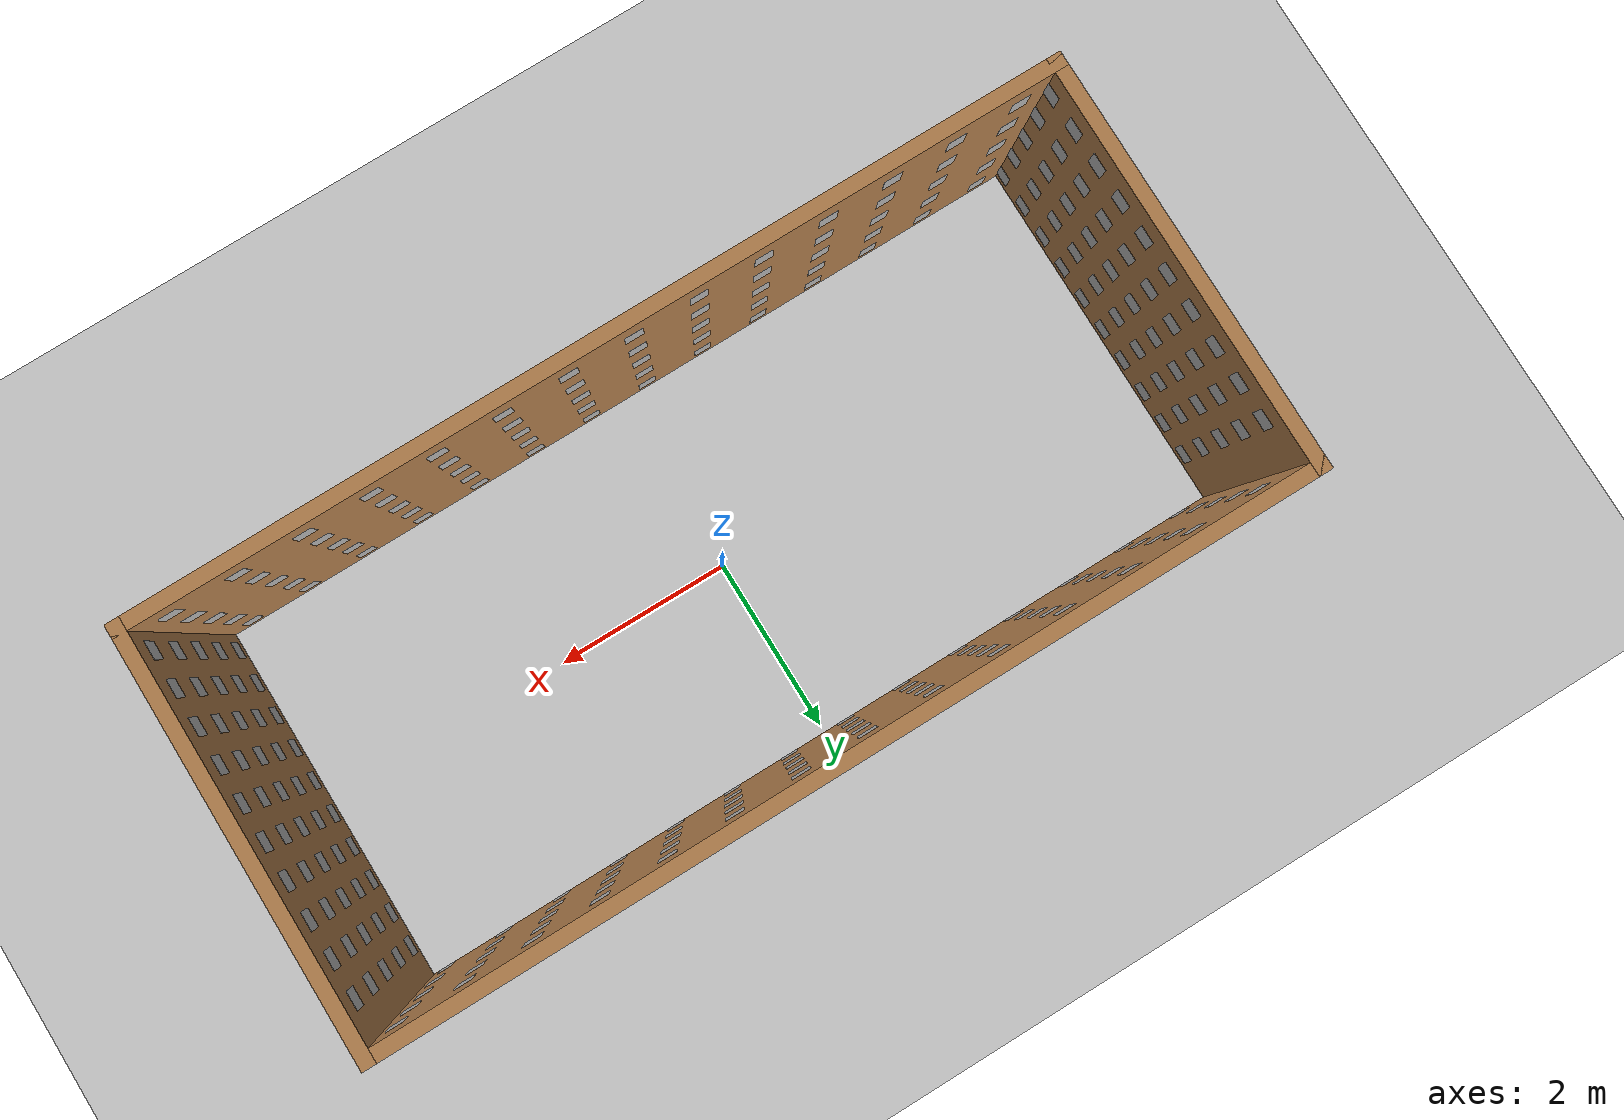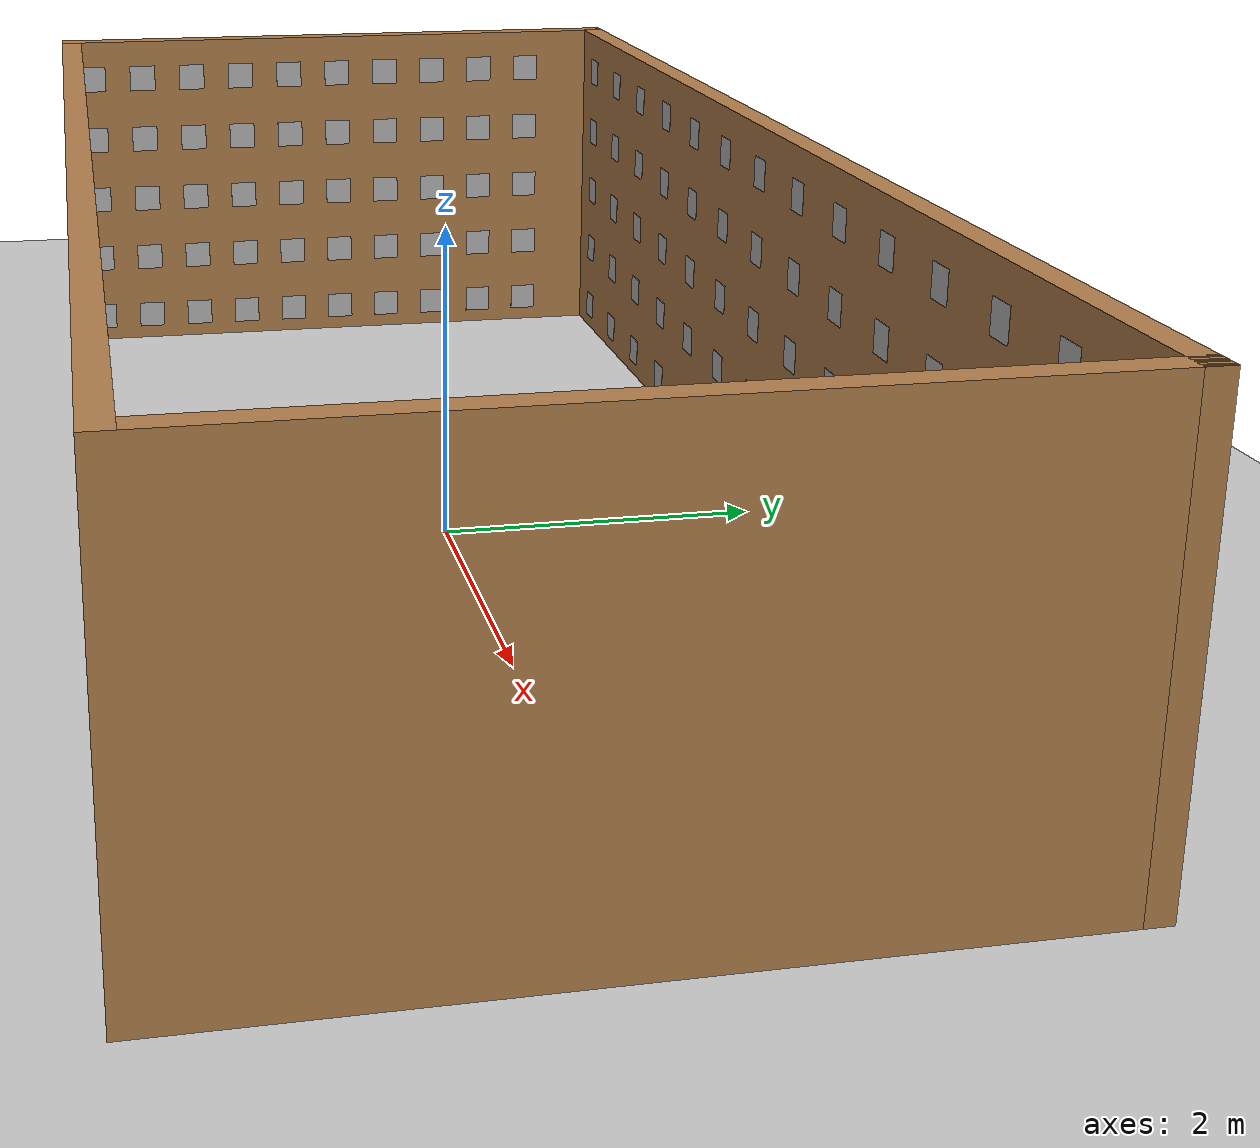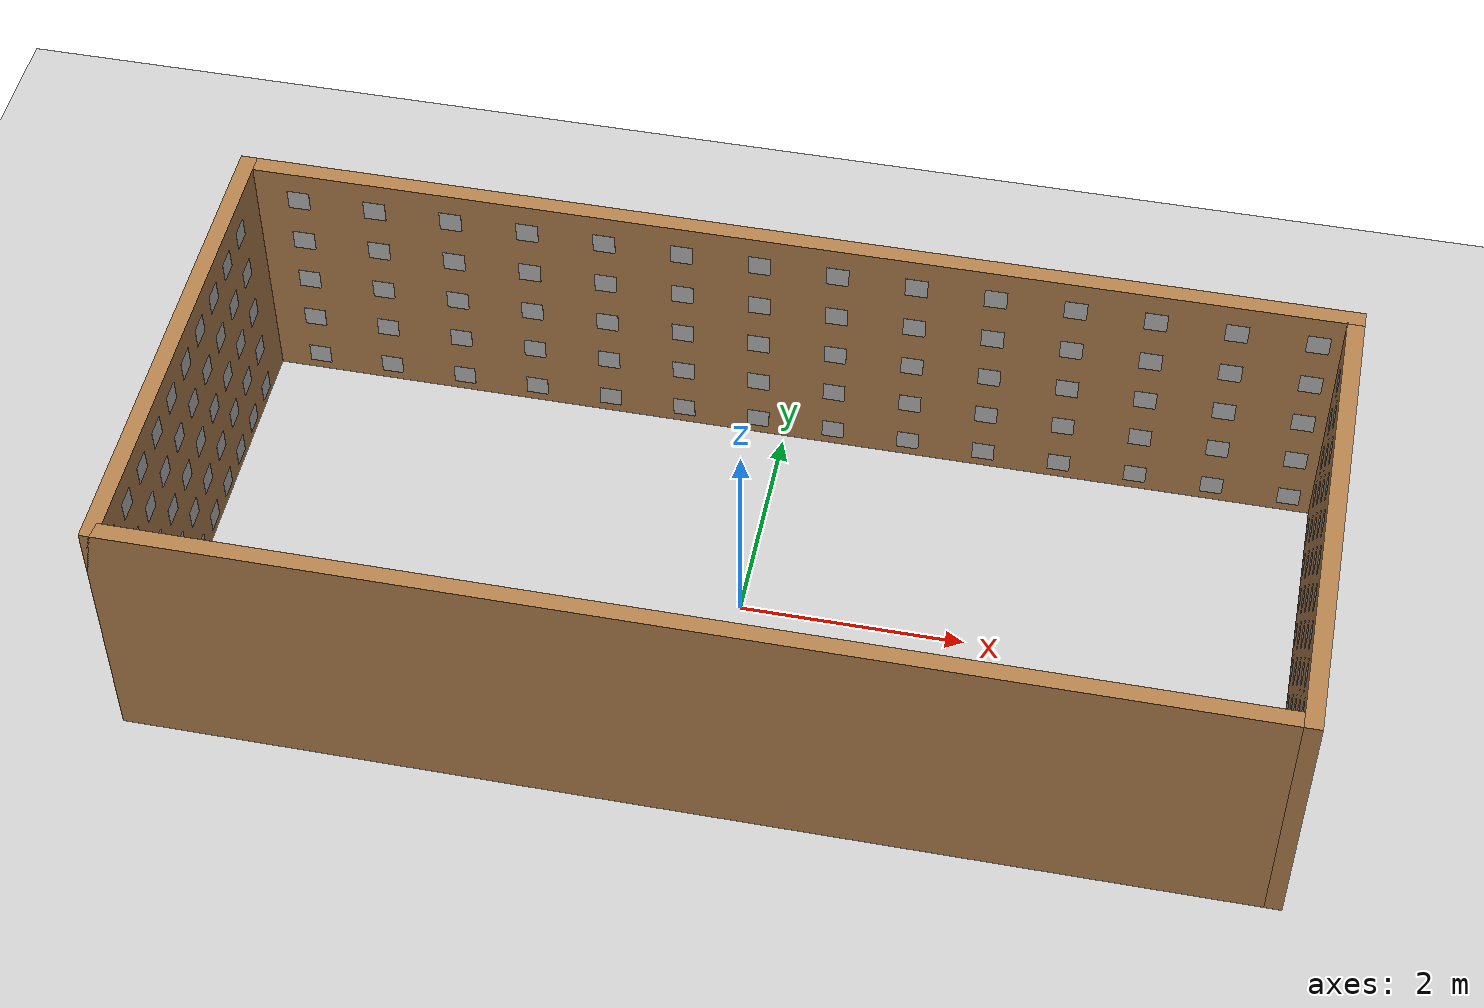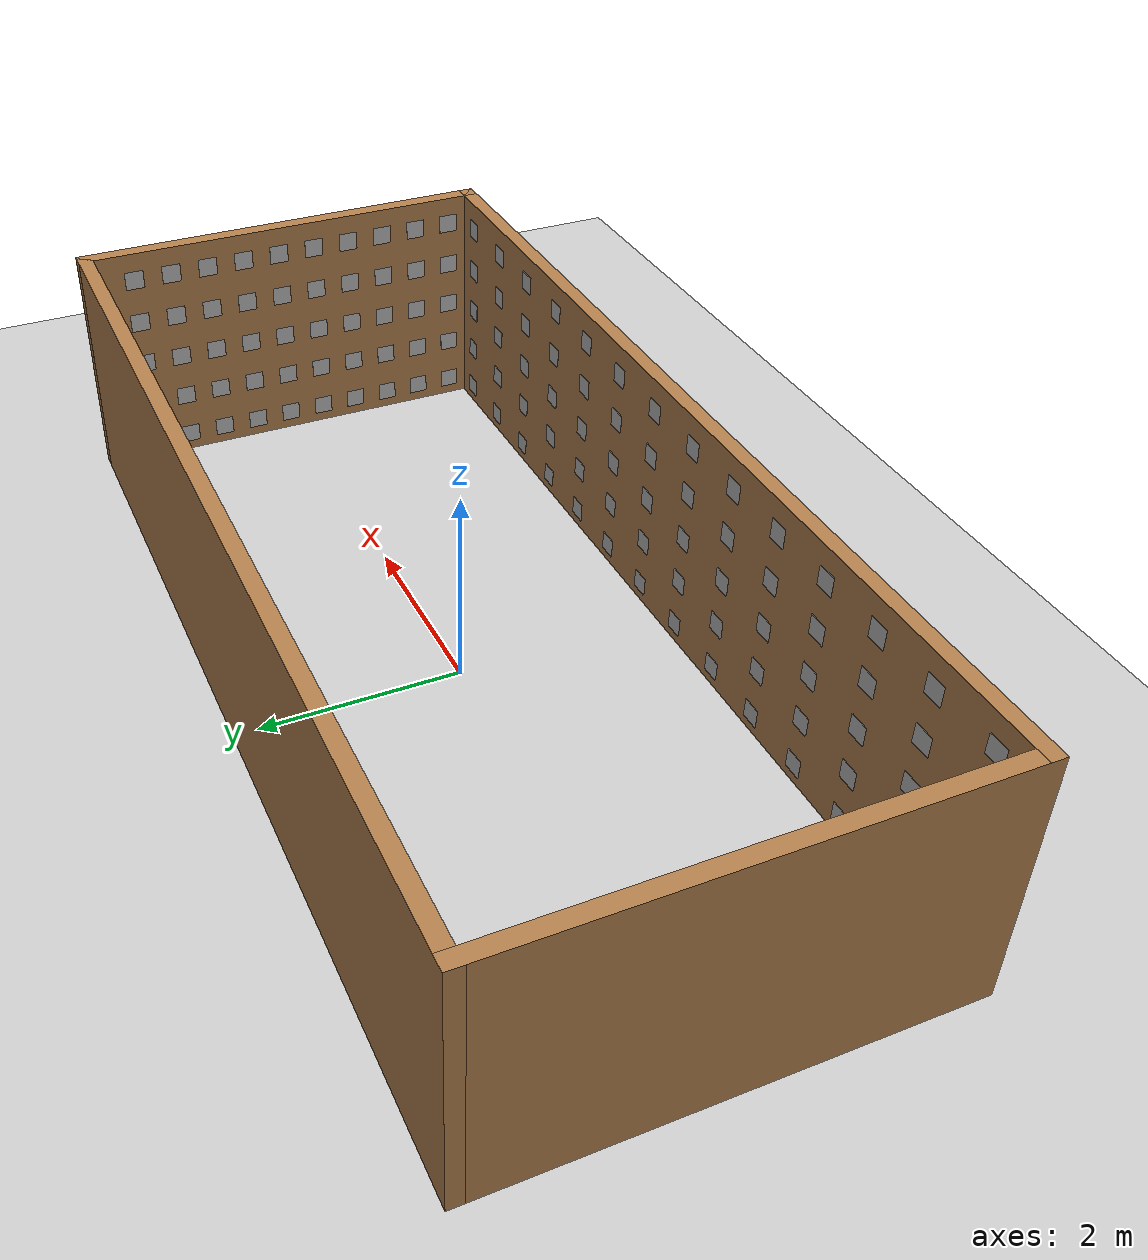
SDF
<sdf version="1.6">
 <world name="default">
  <light name="sun" type="directional">
   <pose>0 0 10 0 -0 0</pose>
   <diffuse>0.8 0.8 0.8 1</diffuse>
   <specular>0.1 0.1 0.1 1</specular>
   <attenuation>
    <range>1000</range>
    <constant>0.9</constant>
    <linear>0.01</linear>
    <quadratic>0.001</quadratic>
   </attenuation>
   <direction>-0.5 0.5 -1</direction>
  </light>
  <model name="ground_plane">
   <static>1</static>
   <link name="link">
    <collision name="collision">
     <geometry><plane><normal>0 0 1</normal><size>100 100</size></plane></geometry>
     <surface><friction><ode><mu>100</mu><mu2>50</mu2></ode></friction></surface>
    </collision>
    <visual name="visual">
     <cast_shadows>0</cast_shadows>
     <geometry><plane><normal>0 0 1</normal><size>100 100</size></plane></geometry>
     <material>
      <script><uri>file://media/materials/scripts/gazebo.material</uri><name>Gazebo/Grey</name></script>
     </material>
    </visual>
   </link>
  </model>
  <gravity>0 0 -9.8</gravity>
  <magnetic_field>6e-06 2.3e-05 -4.2e-05</magnetic_field>
  <atmosphere type="adiabatic"/>
  <physics name="default_physics" default="0" type="ode">
   <max_step_size>0.001</max_step_size>
   <real_time_factor>1</real_time_factor>
   <real_time_update_rate>1000</real_time_update_rate>
  </physics>
  <scene><ambient>0.4 0.4 0.4 1</ambient><background>0.7 0.7 0.7 1</background><shadows>1</shadows></scene>
  <spherical_coordinates>
   <surface_model>EARTH_WGS84</surface_model>
   <latitude_deg>0</latitude_deg>
   <longitude_deg>0</longitude_deg>
   <elevation>0</elevation>
   <heading_deg>0</heading_deg>
  </spherical_coordinates>
  <model name="home1">
   <pose>0.002819 -0.011206 0 0 -0 0</pose>
   <link name="Wall_35">
    <collision name="Wall_35_Collision">
     <geometry><box><size>10 0.15 2.5</size></box></geometry>
     <pose>0 0 1.25 0 -0 0</pose>
    </collision>
    <visual name="Wall_35_Visual">
     <pose>0 0 1.25 0 -0 0</pose>
     <geometry><box><size>10 0.15 2.5</size></box></geometry>
     <material>
      <script><uri>file://media/materials/scripts/gazebo.material</uri><name>Gazebo/Wood</name></script>
      <ambient>1 1 1 1</ambient>
     </material>
    </visual>
    <pose>0 -2.175 0 0 -0 0</pose>
   </link>
   <link name="Wall_36">
    <collision name="Wall_36_Collision">
     <geometry><box><size>4.5 0.15 2.5</size></box></geometry>
     <pose>0 0 1.25 0 -0 0</pose>
    </collision>
    <visual name="Wall_36_Visual">
     <pose>0 0 1.25 0 -0 0</pose>
     <geometry><box><size>4.5 0.15 2.5</size></box></geometry>
     <material>
      <script><uri>file://media/materials/scripts/gazebo.material</uri><name>Gazebo/Wood</name></script>
      <ambient>1 1 1 1</ambient>
     </material>
    </visual>
    <pose>4.925 0 0 0 -0 1.5708</pose>
   </link>
   <link name="Wall_37">
    <collision name="Wall_37_Collision">
     <geometry><box><size>10 0.15 2.5</size></box></geometry>
     <pose>0 0 1.25 0 -0 0</pose>
    </collision>
    <visual name="Wall_37_Visual">
     <pose>0 0 1.25 0 -0 0</pose>
     <geometry><box><size>10 0.15 2.5</size></box></geometry>
     <material>
      <script><uri>file://media/materials/scripts/gazebo.material</uri><name>Gazebo/Wood</name></script>
      <ambient>1 1 1 1</ambient>
     </material>
    </visual>
    <pose>0 2.175 0 0 -0 3.14159</pose>
   </link>
   <link name="Wall_38">
    <collision name="Wall_38_Collision">
     <geometry><box><size>4.5 0.15 2.5</size></box></geometry>
     <pose>0 0 1.25 0 -0 0</pose>
    </collision>
    <visual name="Wall_38_Visual">
     <pose>0 0 1.25 0 -0 0</pose>
     <geometry><box><size>4.5 0.15 2.5</size></box></geometry>
     <material>
      <script><uri>file://media/materials/scripts/gazebo.material</uri><name>Gazebo/Wood</name></script>
      <ambient>1 1 1 1</ambient>
     </material>
    </visual>
    <pose>-4.925 0 0 0 0 -1.5708</pose>
   </link>
   <static>1</static>
  </model>
  <model name="home1_tag">
   <model name="aruco0">
    <static>1</static>
    <link name="link">
     <pose>0 0 0.1 0 -0 0</pose>
     <collision name="collision"><geometry><box><size>0.2 0.001 0.2</size></box></geometry></collision>
     <visual name="visual">
      <cast_shadows>0</cast_shadows>
      <geometry><box><size>0.2 0.001 0.2</size></box></geometry>
      <material>
       <script>
        <uri>model://aruco0/materials/scripts</uri>
        <uri>model://aruco0/materials/textures</uri>
        <name>vrc/aruco0</name>
       </script>
      </material>
     </visual>
    </link>
    <pose>4.95 -1.8 0.1 0 -0 1.57</pose>
   </model>
   <model name="aruco1">
    <static>1</static>
    <link name="link">
     <pose>0 0 0.1 0 -0 0</pose>
     <collision name="collision"><geometry><box><size>0.2 0.001 0.2</size></box></geometry></collision>
     <visual name="visual">
      <cast_shadows>0</cast_shadows>
      <geometry><box><size>0.2 0.001 0.2</size></box></geometry>
      <material>
       <script>
        <uri>model://aruco1/materials/scripts</uri>
        <uri>model://aruco1/materials/textures</uri>
        <name>vrc/aruco1</name>
       </script>
      </material>
     </visual>
    </link>
    <pose>4.95 -1.4 0.1 0 -0 1.57</pose>
   </model>
   <model name="aruco2">
    <static>1</static>
    <link name="link">
     <pose>0 0 0.1 0 -0 0</pose>
     <collision name="collision"><geometry><box><size>0.2 0.001 0.2</size></box></geometry></collision>
     <visual name="visual">
      <cast_shadows>0</cast_shadows>
      <geometry><box><size>0.2 0.001 0.2</size></box></geometry>
      <material>
       <script>
        <uri>model://aruco2/materials/scripts</uri>
        <uri>model://aruco2/materials/textures</uri>
        <name>vrc/aruco2</name>
       </script>
      </material>
     </visual>
    </link>
    <pose>4.95 -1 0.1 0 -0 1.57</pose>
   </model>
   <model name="aruco3">
    <static>1</static>
    <link name="link">
     <pose>0 0 0.1 0 -0 0</pose>
     <collision name="collision"><geometry><box><size>0.2 0.001 0.2</size></box></geometry></collision>
     <visual name="visual">
      <cast_shadows>0</cast_shadows>
      <geometry><box><size>0.2 0.001 0.2</size></box></geometry>
      <material>
       <script>
        <uri>model://aruco3/materials/scripts</uri>
        <uri>model://aruco3/materials/textures</uri>
        <name>vrc/aruco3</name>
       </script>
      </material>
     </visual>
    </link>
    <pose>4.95 -0.6 0.1 0 -0 1.57</pose>
   </model>
   <model name="aruco4">
    <static>1</static>
    <link name="link">
     <pose>0 0 0.1 0 -0 0</pose>
     <collision name="collision"><geometry><box><size>0.2 0.001 0.2</size></box></geometry></collision>
     <visual name="visual">
      <cast_shadows>0</cast_shadows>
      <geometry><box><size>0.2 0.001 0.2</size></box></geometry>
      <material>
       <script>
        <uri>model://aruco4/materials/scripts</uri>
        <uri>model://aruco4/materials/textures</uri>
        <name>vrc/aruco4</name>
       </script>
      </material>
     </visual>
    </link>
    <pose>4.95 -0.2 0.1 0 -0 1.57</pose>
   </model>
   <model name="aruco5">
    <static>1</static>
    <link name="link">
     <pose>0 0 0.1 0 -0 0</pose>
     <collision name="collision"><geometry><box><size>0.2 0.001 0.2</size></box></geometry></collision>
     <visual name="visual">
      <cast_shadows>0</cast_shadows>
      <geometry><box><size>0.2 0.001 0.2</size></box></geometry>
      <material>
       <script>
        <uri>model://aruco5/materials/scripts</uri>
        <uri>model://aruco5/materials/textures</uri>
        <name>vrc/aruco5</name>
       </script>
      </material>
     </visual>
    </link>
    <pose>4.95 0.2 0.1 0 -0 1.57</pose>
   </model>
   <model name="aruco6">
    <static>1</static>
    <link name="link">
     <pose>0 0 0.1 0 -0 0</pose>
     <collision name="collision"><geometry><box><size>0.2 0.001 0.2</size></box></geometry></collision>
     <visual name="visual">
      <cast_shadows>0</cast_shadows>
      <geometry><box><size>0.2 0.001 0.2</size></box></geometry>
      <material>
       <script>
        <uri>model://aruco6/materials/scripts</uri>
        <uri>model://aruco6/materials/textures</uri>
        <name>vrc/aruco6</name>
       </script>
      </material>
     </visual>
    </link>
    <pose>4.95 0.6 0.1 0 -0 1.57</pose>
   </model>
   <model name="aruco7">
    <static>1</static>
    <link name="link">
     <pose>0 0 0.1 0 -0 0</pose>
     <collision name="collision"><geometry><box><size>0.2 0.001 0.2</size></box></geometry></collision>
     <visual name="visual">
      <cast_shadows>0</cast_shadows>
      <geometry><box><size>0.2 0.001 0.2</size></box></geometry>
      <material>
       <script>
        <uri>model://aruco7/materials/scripts</uri>
        <uri>model://aruco7/materials/textures</uri>
        <name>vrc/aruco7</name>
       </script>
      </material>
     </visual>
    </link>
    <pose>4.95 1 0.1 0 -0 1.57</pose>
   </model>
   <model name="aruco8">
    <static>1</static>
    <link name="link">
     <pose>0 0 0.1 0 -0 0</pose>
     <collision name="collision"><geometry><box><size>0.2 0.001 0.2</size></box></geometry></collision>
     <visual name="visual">
      <cast_shadows>0</cast_shadows>
      <geometry><box><size>0.2 0.001 0.2</size></box></geometry>
      <material>
       <script>
        <uri>model://aruco8/materials/scripts</uri>
        <uri>model://aruco8/materials/textures</uri>
        <name>vrc/aruco8</name>
       </script>
      </material>
     </visual>
    </link>
    <pose>4.95 1.4 0.1 0 -0 1.57</pose>
   </model>
   <model name="aruco9">
    <static>1</static>
    <link name="link">
     <pose>0 0 0.1 0 -0 0</pose>
     <collision name="collision"><geometry><box><size>0.2 0.001 0.2</size></box></geometry></collision>
     <visual name="visual">
      <cast_shadows>0</cast_shadows>
      <geometry><box><size>0.2 0.001 0.2</size></box></geometry>
      <material>
       <script>
        <uri>model://aruco9/materials/scripts</uri>
        <uri>model://aruco9/materials/textures</uri>
        <name>vrc/aruco9</name>
       </script>
      </material>
     </visual>
    </link>
    <pose>4.95 1.8 0.1 0 -0 1.57</pose>
   </model>
   <model name="aruco10">
    <static>1</static>
    <link name="link">
     <pose>0 0 0.1 0 -0 0</pose>
     <collision name="collision"><geometry><box><size>0.2 0.001 0.2</size></box></geometry></collision>
     <visual name="visual">
      <cast_shadows>0</cast_shadows>
      <geometry><box><size>0.2 0.001 0.2</size></box></geometry>
      <material>
       <script>
        <uri>model://aruco10/materials/scripts</uri>
        <uri>model://aruco10/materials/textures</uri>
        <name>vrc/aruco10</name>
       </script>
      </material>
     </visual>
    </link>
    <pose>4.95 -1.8 0.6 0 -0 1.57</pose>
   </model>
   <model name="aruco11">
    <static>1</static>
    <link name="link">
     <pose>0 0 0.1 0 -0 0</pose>
     <collision name="collision"><geometry><box><size>0.2 0.001 0.2</size></box></geometry></collision>
     <visual name="visual">
      <cast_shadows>0</cast_shadows>
      <geometry><box><size>0.2 0.001 0.2</size></box></geometry>
      <material>
       <script>
        <uri>model://aruco11/materials/scripts</uri>
        <uri>model://aruco11/materials/textures</uri>
        <name>vrc/aruco11</name>
       </script>
      </material>
     </visual>
    </link>
    <pose>4.95 -1.4 0.6 0 -0 1.57</pose>
   </model>
   <model name="aruco12">
    <static>1</static>
    <link name="link">
     <pose>0 0 0.1 0 -0 0</pose>
     <collision name="collision"><geometry><box><size>0.2 0.001 0.2</size></box></geometry></collision>
     <visual name="visual">
      <cast_shadows>0</cast_shadows>
      <geometry><box><size>0.2 0.001 0.2</size></box></geometry>
      <material>
       <script>
        <uri>model://aruco12/materials/scripts</uri>
        <uri>model://aruco12/materials/textures</uri>
        <name>vrc/aruco12</name>
       </script>
      </material>
     </visual>
    </link>
    <pose>4.95 -1 0.6 0 -0 1.57</pose>
   </model>
   <model name="aruco13">
    <static>1</static>
    <link name="link">
     <pose>0 0 0.1 0 -0 0</pose>
     <collision name="collision"><geometry><box><size>0.2 0.001 0.2</size></box></geometry></collision>
     <visual name="visual">
      <cast_shadows>0</cast_shadows>
      <geometry><box><size>0.2 0.001 0.2</size></box></geometry>
      <material>
       <script>
        <uri>model://aruco13/materials/scripts</uri>
        <uri>model://aruco13/materials/textures</uri>
        <name>vrc/aruco13</name>
       </script>
      </material>
     </visual>
    </link>
    <pose>4.95 -0.6 0.6 0 -0 1.57</pose>
   </model>
   <model name="aruco14">
    <static>1</static>
    <link name="link">
     <pose>0 0 0.1 0 -0 0</pose>
     <collision name="collision"><geometry><box><size>0.2 0.001 0.2</size></box></geometry></collision>
     <visual name="visual">
      <cast_shadows>0</cast_shadows>
      <geometry><box><size>0.2 0.001 0.2</size></box></geometry>
      <material>
       <script>
        <uri>model://aruco14/materials/scripts</uri>
        <uri>model://aruco14/materials/textures</uri>
        <name>vrc/aruco14</name>
       </script>
      </material>
     </visual>
    </link>
    <pose>4.95 -0.2 0.6 0 -0 1.57</pose>
   </model>
   <model name="aruco15">
    <static>1</static>
    <link name="link">
     <pose>0 0 0.1 0 -0 0</pose>
     <collision name="collision"><geometry><box><size>0.2 0.001 0.2</size></box></geometry></collision>
     <visual name="visual">
      <cast_shadows>0</cast_shadows>
      <geometry><box><size>0.2 0.001 0.2</size></box></geometry>
      <material>
       <script>
        <uri>model://aruco15/materials/scripts</uri>
        <uri>model://aruco15/materials/textures</uri>
        <name>vrc/aruco15</name>
       </script>
      </material>
     </visual>
    </link>
    <pose>4.95 0.2 0.6 0 -0 1.57</pose>
   </model>
   <model name="aruco16">
    <static>1</static>
    <link name="link">
     <pose>0 0 0.1 0 -0 0</pose>
     <collision name="collision"><geometry><box><size>0.2 0.001 0.2</size></box></geometry></collision>
     <visual name="visual">
      <cast_shadows>0</cast_shadows>
      <geometry><box><size>0.2 0.001 0.2</size></box></geometry>
      <material>
       <script>
        <uri>model://aruco16/materials/scripts</uri>
        <uri>model://aruco16/materials/textures</uri>
        <name>vrc/aruco16</name>
       </script>
      </material>
     </visual>
    </link>
    <pose>4.95 0.6 0.6 0 -0 1.57</pose>
   </model>
   <model name="aruco17">
    <static>1</static>
    <link name="link">
     <pose>0 0 0.1 0 -0 0</pose>
     <collision name="collision"><geometry><box><size>0.2 0.001 0.2</size></box></geometry></collision>
     <visual name="visual">
      <cast_shadows>0</cast_shadows>
      <geometry><box><size>0.2 0.001 0.2</size></box></geometry>
      <material>
       <script>
        <uri>model://aruco17/materials/scripts</uri>
        <uri>model://aruco17/materials/textures</uri>
        <name>vrc/aruco17</name>
       </script>
      </material>
     </visual>
    </link>
    <pose>4.95 1 0.6 0 -0 1.57</pose>
   </model>
   <model name="aruco18">
    <static>1</static>
    <link name="link">
     <pose>0 0 0.1 0 -0 0</pose>
     <collision name="collision"><geometry><box><size>0.2 0.001 0.2</size></box></geometry></collision>
     <visual name="visual">
      <cast_shadows>0</cast_shadows>
      <geometry><box><size>0.2 0.001 0.2</size></box></geometry>
      <material>
       <script>
        <uri>model://aruco18/materials/scripts</uri>
        <uri>model://aruco18/materials/textures</uri>
        <name>vrc/aruco18</name>
       </script>
      </material>
     </visual>
    </link>
    <pose>4.95 1.4 0.6 0 -0 1.57</pose>
   </model>
   <model name="aruco19">
    <static>1</static>
    <link name="link">
     <pose>0 0 0.1 0 -0 0</pose>
     <collision name="collision"><geometry><box><size>0.2 0.001 0.2</size></box></geometry></collision>
     <visual name="visual">
      <cast_shadows>0</cast_shadows>
      <geometry><box><size>0.2 0.001 0.2</size></box></geometry>
      <material>
       <script>
        <uri>model://aruco19/materials/scripts</uri>
        <uri>model://aruco19/materials/textures</uri>
        <name>vrc/aruco19</name>
       </script>
      </material>
     </visual>
    </link>
    <pose>4.95 1.8 0.6 0 -0 1.57</pose>
   </model>
   <model name="aruco20">
    <static>1</static>
    <link name="link">
     <pose>0 0 0.1 0 -0 0</pose>
     <collision name="collision"><geometry><box><size>0.2 0.001 0.2</size></box></geometry></collision>
     <visual name="visual">
      <cast_shadows>0</cast_shadows>
      <geometry><box><size>0.2 0.001 0.2</size></box></geometry>
      <material>
       <script>
        <uri>model://aruco20/materials/scripts</uri>
        <uri>model://aruco20/materials/textures</uri>
        <name>vrc/aruco20</name>
       </script>
      </material>
     </visual>
    </link>
    <pose>4.95 -1.8 1.1 0 -0 1.57</pose>
   </model>
   <model name="aruco21">
    <static>1</static>
    <link name="link">
     <pose>0 0 0.1 0 -0 0</pose>
     <collision name="collision"><geometry><box><size>0.2 0.001 0.2</size></box></geometry></collision>
     <visual name="visual">
      <cast_shadows>0</cast_shadows>
      <geometry><box><size>0.2 0.001 0.2</size></box></geometry>
      <material>
       <script>
        <uri>model://aruco21/materials/scripts</uri>
        <uri>model://aruco21/materials/textures</uri>
        <name>vrc/aruco21</name>
       </script>
      </material>
     </visual>
    </link>
    <pose>4.95 -1.4 1.1 0 -0 1.57</pose>
   </model>
   <model name="aruco22">
    <static>1</static>
    <link name="link">
     <pose>0 0 0.1 0 -0 0</pose>
     <collision name="collision"><geometry><box><size>0.2 0.001 0.2</size></box></geometry></collision>
     <visual name="visual">
      <cast_shadows>0</cast_shadows>
      <geometry><box><size>0.2 0.001 0.2</size></box></geometry>
      <material>
       <script>
        <uri>model://aruco22/materials/scripts</uri>
        <uri>model://aruco22/materials/textures</uri>
        <name>vrc/aruco22</name>
       </script>
      </material>
     </visual>
    </link>
    <pose>4.95 -1 1.1 0 -0 1.57</pose>
   </model>
   <model name="aruco23">
    <static>1</static>
    <link name="link">
     <pose>0 0 0.1 0 -0 0</pose>
     <collision name="collision"><geometry><box><size>0.2 0.001 0.2</size></box></geometry></collision>
     <visual name="visual">
      <cast_shadows>0</cast_shadows>
      <geometry><box><size>0.2 0.001 0.2</size></box></geometry>
      <material>
       <script>
        <uri>model://aruco23/materials/scripts</uri>
        <uri>model://aruco23/materials/textures</uri>
        <name>vrc/aruco23</name>
       </script>
      </material>
     </visual>
    </link>
    <pose>4.95 -0.6 1.1 0 -0 1.57</pose>
   </model>
   <model name="aruco24">
    <static>1</static>
    <link name="link">
     <pose>0 0 0.1 0 -0 0</pose>
     <collision name="collision"><geometry><box><size>0.2 0.001 0.2</size></box></geometry></collision>
     <visual name="visual">
      <cast_shadows>0</cast_shadows>
      <geometry><box><size>0.2 0.001 0.2</size></box></geometry>
      <material>
       <script>
        <uri>model://aruco24/materials/scripts</uri>
        <uri>model://aruco24/materials/textures</uri>
        <name>vrc/aruco24</name>
       </script>
      </material>
     </visual>
    </link>
    <pose>4.95 -0.2 1.1 0 -0 1.57</pose>
   </model>
   <model name="aruco25">
    <static>1</static>
    <link name="link">
     <pose>0 0 0.1 0 -0 0</pose>
     <collision name="collision"><geometry><box><size>0.2 0.001 0.2</size></box></geometry></collision>
     <visual name="visual">
      <cast_shadows>0</cast_shadows>
      <geometry><box><size>0.2 0.001 0.2</size></box></geometry>
      <material>
       <script>
        <uri>model://aruco25/materials/scripts</uri>
        <uri>model://aruco25/materials/textures</uri>
        <name>vrc/aruco25</name>
       </script>
      </material>
     </visual>
    </link>
    <pose>4.95 0.2 1.1 0 -0 1.57</pose>
   </model>
   <model name="aruco26">
    <static>1</static>
    <link name="link">
     <pose>0 0 0.1 0 -0 0</pose>
     <collision name="collision"><geometry><box><size>0.2 0.001 0.2</size></box></geometry></collision>
     <visual name="visual">
      <cast_shadows>0</cast_shadows>
      <geometry><box><size>0.2 0.001 0.2</size></box></geometry>
      <material>
       <script>
        <uri>model://aruco26/materials/scripts</uri>
        <uri>model://aruco26/materials/textures</uri>
        <name>vrc/aruco26</name>
       </script>
      </material>
     </visual>
    </link>
    <pose>4.95 0.6 1.1 0 -0 1.57</pose>
   </model>
   <model name="aruco27">
    <static>1</static>
    <link name="link">
     <pose>0 0 0.1 0 -0 0</pose>
     <collision name="collision"><geometry><box><size>0.2 0.001 0.2</size></box></geometry></collision>
     <visual name="visual">
      <cast_shadows>0</cast_shadows>
      <geometry><box><size>0.2 0.001 0.2</size></box></geometry>
      <material>
       <script>
        <uri>model://aruco27/materials/scripts</uri>
        <uri>model://aruco27/materials/textures</uri>
        <name>vrc/aruco27</name>
       </script>
      </material>
     </visual>
    </link>
    <pose>4.95 1 1.1 0 -0 1.57</pose>
   </model>
   <model name="aruco28">
    <static>1</static>
    <link name="link">
     <pose>0 0 0.1 0 -0 0</pose>
     <collision name="collision"><geometry><box><size>0.2 0.001 0.2</size></box></geometry></collision>
     <visual name="visual">
      <cast_shadows>0</cast_shadows>
      <geometry><box><size>0.2 0.001 0.2</size></box></geometry>
      <material>
       <script>
        <uri>model://aruco28/materials/scripts</uri>
        <uri>model://aruco28/materials/textures</uri>
        <name>vrc/aruco28</name>
       </script>
      </material>
     </visual>
    </link>
    <pose>4.95 1.4 1.1 0 -0 1.57</pose>
   </model>
   <model name="aruco29">
    <static>1</static>
    <link name="link">
     <pose>0 0 0.1 0 -0 0</pose>
     <collision name="collision"><geometry><box><size>0.2 0.001 0.2</size></box></geometry></collision>
     <visual name="visual">
      <cast_shadows>0</cast_shadows>
      <geometry><box><size>0.2 0.001 0.2</size></box></geometry>
      <material>
       <script>
        <uri>model://aruco29/materials/scripts</uri>
        <uri>model://aruco29/materials/textures</uri>
        <name>vrc/aruco29</name>
       </script>
      </material>
     </visual>
    </link>
    <pose>4.95 1.8 1.1 0 -0 1.57</pose>
   </model>
   <model name="aruco30">
    <static>1</static>
    <link name="link">
     <pose>0 0 0.1 0 -0 0</pose>
     <collision name="collision"><geometry><box><size>0.2 0.001 0.2</size></box></geometry></collision>
     <visual name="visual">
      <cast_shadows>0</cast_shadows>
      <geometry><box><size>0.2 0.001 0.2</size></box></geometry>
      <material>
       <script>
        <uri>model://aruco30/materials/scripts</uri>
        <uri>model://aruco30/materials/textures</uri>
        <name>vrc/aruco30</name>
       </script>
      </material>
     </visual>
    </link>
    <pose>4.95 -1.8 1.6 0 -0 1.57</pose>
   </model>
   <model name="aruco31">
    <static>1</static>
    <link name="link">
     <pose>0 0 0.1 0 -0 0</pose>
     <collision name="collision"><geometry><box><size>0.2 0.001 0.2</size></box></geometry></collision>
     <visual name="visual">
      <cast_shadows>0</cast_shadows>
      <geometry><box><size>0.2 0.001 0.2</size></box></geometry>
      <material>
       <script>
        <uri>model://aruco31/materials/scripts</uri>
        <uri>model://aruco31/materials/textures</uri>
        <name>vrc/aruco31</name>
       </script>
      </material>
     </visual>
    </link>
    <pose>4.95 -1.4 1.6 0 -0 1.57</pose>
   </model>
   <model name="aruco32">
    <static>1</static>
    <link name="link">
     <pose>0 0 0.1 0 -0 0</pose>
     <collision name="collision"><geometry><box><size>0.2 0.001 0.2</size></box></geometry></collision>
     <visual name="visual">
      <cast_shadows>0</cast_shadows>
      <geometry><box><size>0.2 0.001 0.2</size></box></geometry>
      <material>
       <script>
        <uri>model://aruco32/materials/scripts</uri>
        <uri>model://aruco32/materials/textures</uri>
        <name>vrc/aruco32</name>
       </script>
      </material>
     </visual>
    </link>
    <pose>4.95 -1 1.6 0 -0 1.57</pose>
   </model>
   <model name="aruco33">
    <static>1</static>
    <link name="link">
     <pose>0 0 0.1 0 -0 0</pose>
     <collision name="collision"><geometry><box><size>0.2 0.001 0.2</size></box></geometry></collision>
     <visual name="visual">
      <cast_shadows>0</cast_shadows>
      <geometry><box><size>0.2 0.001 0.2</size></box></geometry>
      <material>
       <script>
        <uri>model://aruco33/materials/scripts</uri>
        <uri>model://aruco33/materials/textures</uri>
        <name>vrc/aruco33</name>
       </script>
      </material>
     </visual>
    </link>
    <pose>4.95 -0.6 1.6 0 -0 1.57</pose>
   </model>
   <model name="aruco34">
    <static>1</static>
    <link name="link">
     <pose>0 0 0.1 0 -0 0</pose>
     <collision name="collision"><geometry><box><size>0.2 0.001 0.2</size></box></geometry></collision>
     <visual name="visual">
      <cast_shadows>0</cast_shadows>
      <geometry><box><size>0.2 0.001 0.2</size></box></geometry>
      <material>
       <script>
        <uri>model://aruco34/materials/scripts</uri>
        <uri>model://aruco34/materials/textures</uri>
        <name>vrc/aruco34</name>
       </script>
      </material>
     </visual>
    </link>
    <pose>4.95 -0.2 1.6 0 -0 1.57</pose>
   </model>
   <model name="aruco35">
    <static>1</static>
    <link name="link">
     <pose>0 0 0.1 0 -0 0</pose>
     <collision name="collision"><geometry><box><size>0.2 0.001 0.2</size></box></geometry></collision>
     <visual name="visual">
      <cast_shadows>0</cast_shadows>
      <geometry><box><size>0.2 0.001 0.2</size></box></geometry>
      <material>
       <script>
        <uri>model://aruco35/materials/scripts</uri>
        <uri>model://aruco35/materials/textures</uri>
        <name>vrc/aruco35</name>
       </script>
      </material>
     </visual>
    </link>
    <pose>4.95 0.2 1.6 0 -0 1.57</pose>
   </model>
   <model name="aruco36">
    <static>1</static>
    <link name="link">
     <pose>0 0 0.1 0 -0 0</pose>
     <collision name="collision"><geometry><box><size>0.2 0.001 0.2</size></box></geometry></collision>
     <visual name="visual">
      <cast_shadows>0</cast_shadows>
      <geometry><box><size>0.2 0.001 0.2</size></box></geometry>
      <material>
       <script>
        <uri>model://aruco36/materials/scripts</uri>
        <uri>model://aruco36/materials/textures</uri>
        <name>vrc/aruco36</name>
       </script>
      </material>
     </visual>
    </link>
    <pose>4.95 0.6 1.6 0 -0 1.57</pose>
   </model>
   <model name="aruco37">
    <static>1</static>
    <link name="link">
     <pose>0 0 0.1 0 -0 0</pose>
     <collision name="collision"><geometry><box><size>0.2 0.001 0.2</size></box></geometry></collision>
     <visual name="visual">
      <cast_shadows>0</cast_shadows>
      <geometry><box><size>0.2 0.001 0.2</size></box></geometry>
      <material>
       <script>
        <uri>model://aruco37/materials/scripts</uri>
        <uri>model://aruco37/materials/textures</uri>
        <name>vrc/aruco37</name>
       </script>
      </material>
     </visual>
    </link>
    <pose>4.95 1 1.6 0 -0 1.57</pose>
   </model>
   <model name="aruco38">
    <static>1</static>
    <link name="link">
     <pose>0 0 0.1 0 -0 0</pose>
     <collision name="collision"><geometry><box><size>0.2 0.001 0.2</size></box></geometry></collision>
     <visual name="visual">
      <cast_shadows>0</cast_shadows>
      <geometry><box><size>0.2 0.001 0.2</size></box></geometry>
      <material>
       <script>
        <uri>model://aruco38/materials/scripts</uri>
        <uri>model://aruco38/materials/textures</uri>
        <name>vrc/aruco38</name>
       </script>
      </material>
     </visual>
    </link>
    <pose>4.95 1.4 1.6 0 -0 1.57</pose>
   </model>
   <model name="aruco39">
    <static>1</static>
    <link name="link">
     <pose>0 0 0.1 0 -0 0</pose>
     <collision name="collision"><geometry><box><size>0.2 0.001 0.2</size></box></geometry></collision>
     <visual name="visual">
      <cast_shadows>0</cast_shadows>
      <geometry><box><size>0.2 0.001 0.2</size></box></geometry>
      <material>
       <script>
        <uri>model://aruco39/materials/scripts</uri>
        <uri>model://aruco39/materials/textures</uri>
        <name>vrc/aruco39</name>
       </script>
      </material>
     </visual>
    </link>
    <pose>4.95 1.8 1.6 0 -0 1.57</pose>
   </model>
   <model name="aruco40">
    <static>1</static>
    <link name="link">
     <pose>0 0 0.1 0 -0 0</pose>
     <collision name="collision"><geometry><box><size>0.2 0.001 0.2</size></box></geometry></collision>
     <visual name="visual">
      <cast_shadows>0</cast_shadows>
      <geometry><box><size>0.2 0.001 0.2</size></box></geometry>
      <material>
       <script>
        <uri>model://aruco40/materials/scripts</uri>
        <uri>model://aruco40/materials/textures</uri>
        <name>vrc/aruco40</name>
       </script>
      </material>
     </visual>
    </link>
    <pose>4.95 -1.8 2.1 0 -0 1.57</pose>
   </model>
   <model name="aruco41">
    <static>1</static>
    <link name="link">
     <pose>0 0 0.1 0 -0 0</pose>
     <collision name="collision"><geometry><box><size>0.2 0.001 0.2</size></box></geometry></collision>
     <visual name="visual">
      <cast_shadows>0</cast_shadows>
      <geometry><box><size>0.2 0.001 0.2</size></box></geometry>
      <material>
       <script>
        <uri>model://aruco41/materials/scripts</uri>
        <uri>model://aruco41/materials/textures</uri>
        <name>vrc/aruco41</name>
       </script>
      </material>
     </visual>
    </link>
    <pose>4.95 -1.4 2.1 0 -0 1.57</pose>
   </model>
   <model name="aruco42">
    <static>1</static>
    <link name="link">
     <pose>0 0 0.1 0 -0 0</pose>
     <collision name="collision"><geometry><box><size>0.2 0.001 0.2</size></box></geometry></collision>
     <visual name="visual">
      <cast_shadows>0</cast_shadows>
      <geometry><box><size>0.2 0.001 0.2</size></box></geometry>
      <material>
       <script>
        <uri>model://aruco42/materials/scripts</uri>
        <uri>model://aruco42/materials/textures</uri>
        <name>vrc/aruco42</name>
       </script>
      </material>
     </visual>
    </link>
    <pose>4.95 -1 2.1 0 -0 1.57</pose>
   </model>
   <model name="aruco43">
    <static>1</static>
    <link name="link">
     <pose>0 0 0.1 0 -0 0</pose>
     <collision name="collision"><geometry><box><size>0.2 0.001 0.2</size></box></geometry></collision>
     <visual name="visual">
      <cast_shadows>0</cast_shadows>
      <geometry><box><size>0.2 0.001 0.2</size></box></geometry>
      <material>
       <script>
        <uri>model://aruco43/materials/scripts</uri>
        <uri>model://aruco43/materials/textures</uri>
        <name>vrc/aruco43</name>
       </script>
      </material>
     </visual>
    </link>
    <pose>4.95 -0.6 2.1 0 -0 1.57</pose>
   </model>
   <model name="aruco44">
    <static>1</static>
    <link name="link">
     <pose>0 0 0.1 0 -0 0</pose>
     <collision name="collision"><geometry><box><size>0.2 0.001 0.2</size></box></geometry></collision>
     <visual name="visual">
      <cast_shadows>0</cast_shadows>
      <geometry><box><size>0.2 0.001 0.2</size></box></geometry>
      <material>
       <script>
        <uri>model://aruco44/materials/scripts</uri>
        <uri>model://aruco44/materials/textures</uri>
        <name>vrc/aruco44</name>
       </script>
      </material>
     </visual>
    </link>
    <pose>4.95 -0.2 2.1 0 -0 1.57</pose>
   </model>
   <model name="aruco45">
    <static>1</static>
    <link name="link">
     <pose>0 0 0.1 0 -0 0</pose>
     <collision name="collision"><geometry><box><size>0.2 0.001 0.2</size></box></geometry></collision>
     <visual name="visual">
      <cast_shadows>0</cast_shadows>
      <geometry><box><size>0.2 0.001 0.2</size></box></geometry>
      <material>
       <script>
        <uri>model://aruco45/materials/scripts</uri>
        <uri>model://aruco45/materials/textures</uri>
        <name>vrc/aruco45</name>
       </script>
      </material>
     </visual>
    </link>
    <pose>4.95 0.2 2.1 0 -0 1.57</pose>
   </model>
   <model name="aruco46">
    <static>1</static>
    <link name="link">
     <pose>0 0 0.1 0 -0 0</pose>
     <collision name="collision"><geometry><box><size>0.2 0.001 0.2</size></box></geometry></collision>
     <visual name="visual">
      <cast_shadows>0</cast_shadows>
      <geometry><box><size>0.2 0.001 0.2</size></box></geometry>
      <material>
       <script>
        <uri>model://aruco46/materials/scripts</uri>
        <uri>model://aruco46/materials/textures</uri>
        <name>vrc/aruco46</name>
       </script>
      </material>
     </visual>
    </link>
    <pose>4.95 0.6 2.1 0 -0 1.57</pose>
   </model>
   <model name="aruco47">
    <static>1</static>
    <link name="link">
     <pose>0 0 0.1 0 -0 0</pose>
     <collision name="collision"><geometry><box><size>0.2 0.001 0.2</size></box></geometry></collision>
     <visual name="visual">
      <cast_shadows>0</cast_shadows>
      <geometry><box><size>0.2 0.001 0.2</size></box></geometry>
      <material>
       <script>
        <uri>model://aruco47/materials/scripts</uri>
        <uri>model://aruco47/materials/textures</uri>
        <name>vrc/aruco47</name>
       </script>
      </material>
     </visual>
    </link>
    <pose>4.95 1 2.1 0 -0 1.57</pose>
   </model>
   <model name="aruco48">
    <static>1</static>
    <link name="link">
     <pose>0 0 0.1 0 -0 0</pose>
     <collision name="collision"><geometry><box><size>0.2 0.001 0.2</size></box></geometry></collision>
     <visual name="visual">
      <cast_shadows>0</cast_shadows>
      <geometry><box><size>0.2 0.001 0.2</size></box></geometry>
      <material>
       <script>
        <uri>model://aruco48/materials/scripts</uri>
        <uri>model://aruco48/materials/textures</uri>
        <name>vrc/aruco48</name>
       </script>
      </material>
     </visual>
    </link>
    <pose>4.95 1.4 2.1 0 -0 1.57</pose>
   </model>
   <model name="aruco49">
    <static>1</static>
    <link name="link">
     <pose>0 0 0.1 0 -0 0</pose>
     <collision name="collision"><geometry><box><size>0.2 0.001 0.2</size></box></geometry></collision>
     <visual name="visual">
      <cast_shadows>0</cast_shadows>
      <geometry><box><size>0.2 0.001 0.2</size></box></geometry>
      <material>
       <script>
        <uri>model://aruco49/materials/scripts</uri>
        <uri>model://aruco49/materials/textures</uri>
        <name>vrc/aruco49</name>
       </script>
      </material>
     </visual>
    </link>
    <pose>4.95 1.8 2.1 0 -0 1.57</pose>
   </model>
   <static>0</static>
   <pose>-0.100901 -0.109509 0 0 -0 0</pose>
  </model>
  <model name="home1_tag2">
   <model name="aruco50">
    <static>1</static>
    <link name="link">
     <pose>0 0 0.1 0 -0 0</pose>
     <collision name="collision"><geometry><box><size>0.2 0.001 0.2</size></box></geometry></collision>
     <visual name="visual">
      <cast_shadows>0</cast_shadows>
      <geometry><box><size>0.2 0.001 0.2</size></box></geometry>
      <material>
       <script>
        <uri>model://aruco50/materials/scripts</uri>
        <uri>model://aruco50/materials/textures</uri>
        <name>vrc/aruco50</name>
       </script>
      </material>
     </visual>
    </link>
    <pose>4.95 -1.8 0.1 0 0 -1.57</pose>
   </model>
   <model name="aruco51">
    <static>1</static>
    <link name="link">
     <pose>0 0 0.1 0 -0 0</pose>
     <collision name="collision"><geometry><box><size>0.2 0.001 0.2</size></box></geometry></collision>
     <visual name="visual">
      <cast_shadows>0</cast_shadows>
      <geometry><box><size>0.2 0.001 0.2</size></box></geometry>
      <material>
       <script>
        <uri>model://aruco51/materials/scripts</uri>
        <uri>model://aruco51/materials/textures</uri>
        <name>vrc/aruco51</name>
       </script>
      </material>
     </visual>
    </link>
    <pose>4.95 -1.4 0.1 0 0 -1.57</pose>
   </model>
   <model name="aruco52">
    <static>1</static>
    <link name="link">
     <pose>0 0 0.1 0 -0 0</pose>
     <collision name="collision"><geometry><box><size>0.2 0.001 0.2</size></box></geometry></collision>
     <visual name="visual">
      <cast_shadows>0</cast_shadows>
      <geometry><box><size>0.2 0.001 0.2</size></box></geometry>
      <material>
       <script>
        <uri>model://aruco52/materials/scripts</uri>
        <uri>model://aruco52/materials/textures</uri>
        <name>vrc/aruco52</name>
       </script>
      </material>
     </visual>
    </link>
    <pose>4.95 -1 0.1 0 0 -1.57</pose>
   </model>
   <model name="aruco53">
    <static>1</static>
    <link name="link">
     <pose>0 0 0.1 0 -0 0</pose>
     <collision name="collision"><geometry><box><size>0.2 0.001 0.2</size></box></geometry></collision>
     <visual name="visual">
      <cast_shadows>0</cast_shadows>
      <geometry><box><size>0.2 0.001 0.2</size></box></geometry>
      <material>
       <script>
        <uri>model://aruco53/materials/scripts</uri>
        <uri>model://aruco53/materials/textures</uri>
        <name>vrc/aruco53</name>
       </script>
      </material>
     </visual>
    </link>
    <pose>4.95 -0.6 0.1 0 0 -1.57</pose>
   </model>
   <model name="aruco54">
    <static>1</static>
    <link name="link">
     <pose>0 0 0.1 0 -0 0</pose>
     <collision name="collision"><geometry><box><size>0.2 0.001 0.2</size></box></geometry></collision>
     <visual name="visual">
      <cast_shadows>0</cast_shadows>
      <geometry><box><size>0.2 0.001 0.2</size></box></geometry>
      <material>
       <script>
        <uri>model://aruco54/materials/scripts</uri>
        <uri>model://aruco54/materials/textures</uri>
        <name>vrc/aruco54</name>
       </script>
      </material>
     </visual>
    </link>
    <pose>4.95 -0.2 0.1 0 0 -1.57</pose>
   </model>
   <model name="aruco55">
    <static>1</static>
    <link name="link">
     <pose>0 0 0.1 0 -0 0</pose>
     <collision name="collision"><geometry><box><size>0.2 0.001 0.2</size></box></geometry></collision>
     <visual name="visual">
      <cast_shadows>0</cast_shadows>
      <geometry><box><size>0.2 0.001 0.2</size></box></geometry>
      <material>
       <script>
        <uri>model://aruco55/materials/scripts</uri>
        <uri>model://aruco55/materials/textures</uri>
        <name>vrc/aruco55</name>
       </script>
      </material>
     </visual>
    </link>
    <pose>4.95 0.2 0.1 0 0 -1.57</pose>
   </model>
   <model name="aruco56">
    <static>1</static>
    <link name="link">
     <pose>0 0 0.1 0 -0 0</pose>
     <collision name="collision"><geometry><box><size>0.2 0.001 0.2</size></box></geometry></collision>
     <visual name="visual">
      <cast_shadows>0</cast_shadows>
      <geometry><box><size>0.2 0.001 0.2</size></box></geometry>
      <material>
       <script>
        <uri>model://aruco56/materials/scripts</uri>
        <uri>model://aruco56/materials/textures</uri>
        <name>vrc/aruco56</name>
       </script>
      </material>
     </visual>
    </link>
    <pose>4.95 0.6 0.1 0 0 -1.57</pose>
   </model>
   <model name="aruco57">
    <static>1</static>
    <link name="link">
     <pose>0 0 0.1 0 -0 0</pose>
     <collision name="collision"><geometry><box><size>0.2 0.001 0.2</size></box></geometry></collision>
     <visual name="visual">
      <cast_shadows>0</cast_shadows>
      <geometry><box><size>0.2 0.001 0.2</size></box></geometry>
      <material>
       <script>
        <uri>model://aruco57/materials/scripts</uri>
        <uri>model://aruco57/materials/textures</uri>
        <name>vrc/aruco57</name>
       </script>
      </material>
     </visual>
    </link>
    <pose>4.95 1 0.1 0 0 -1.57</pose>
   </model>
   <model name="aruco58">
    <static>1</static>
    <link name="link">
     <pose>0 0 0.1 0 -0 0</pose>
     <collision name="collision"><geometry><box><size>0.2 0.001 0.2</size></box></geometry></collision>
     <visual name="visual">
      <cast_shadows>0</cast_shadows>
      <geometry><box><size>0.2 0.001 0.2</size></box></geometry>
      <material>
       <script>
        <uri>model://aruco58/materials/scripts</uri>
        <uri>model://aruco58/materials/textures</uri>
        <name>vrc/aruco58</name>
       </script>
      </material>
     </visual>
    </link>
    <pose>4.95 1.4 0.1 0 0 -1.57</pose>
   </model>
   <model name="aruco59">
    <static>1</static>
    <link name="link">
     <pose>0 0 0.1 0 -0 0</pose>
     <collision name="collision"><geometry><box><size>0.2 0.001 0.2</size></box></geometry></collision>
     <visual name="visual">
      <cast_shadows>0</cast_shadows>
      <geometry><box><size>0.2 0.001 0.2</size></box></geometry>
      <material>
       <script>
        <uri>model://aruco59/materials/scripts</uri>
        <uri>model://aruco59/materials/textures</uri>
        <name>vrc/aruco59</name>
       </script>
      </material>
     </visual>
    </link>
    <pose>4.95 1.8 0.1 0 0 -1.57</pose>
   </model>
   <model name="aruco60">
    <static>1</static>
    <link name="link">
     <pose>0 0 0.1 0 -0 0</pose>
     <collision name="collision"><geometry><box><size>0.2 0.001 0.2</size></box></geometry></collision>
     <visual name="visual">
      <cast_shadows>0</cast_shadows>
      <geometry><box><size>0.2 0.001 0.2</size></box></geometry>
      <material>
       <script>
        <uri>model://aruco60/materials/scripts</uri>
        <uri>model://aruco60/materials/textures</uri>
        <name>vrc/aruco60</name>
       </script>
      </material>
     </visual>
    </link>
    <pose>4.95 -1.8 0.6 0 0 -1.57</pose>
   </model>
   <model name="aruco61">
    <static>1</static>
    <link name="link">
     <pose>0 0 0.1 0 -0 0</pose>
     <collision name="collision"><geometry><box><size>0.2 0.001 0.2</size></box></geometry></collision>
     <visual name="visual">
      <cast_shadows>0</cast_shadows>
      <geometry><box><size>0.2 0.001 0.2</size></box></geometry>
      <material>
       <script>
        <uri>model://aruco61/materials/scripts</uri>
        <uri>model://aruco61/materials/textures</uri>
        <name>vrc/aruco61</name>
       </script>
      </material>
     </visual>
    </link>
    <pose>4.95 -1.4 0.6 0 0 -1.57</pose>
   </model>
   <model name="aruco62">
    <static>1</static>
    <link name="link">
     <pose>0 0 0.1 0 -0 0</pose>
     <collision name="collision"><geometry><box><size>0.2 0.001 0.2</size></box></geometry></collision>
     <visual name="visual">
      <cast_shadows>0</cast_shadows>
      <geometry><box><size>0.2 0.001 0.2</size></box></geometry>
      <material>
       <script>
        <uri>model://aruco62/materials/scripts</uri>
        <uri>model://aruco62/materials/textures</uri>
        <name>vrc/aruco62</name>
       </script>
      </material>
     </visual>
    </link>
    <pose>4.95 -1 0.6 0 0 -1.57</pose>
   </model>
   <model name="aruco63">
    <static>1</static>
    <link name="link">
     <pose>0 0 0.1 0 -0 0</pose>
     <collision name="collision"><geometry><box><size>0.2 0.001 0.2</size></box></geometry></collision>
     <visual name="visual">
      <cast_shadows>0</cast_shadows>
      <geometry><box><size>0.2 0.001 0.2</size></box></geometry>
      <material>
       <script>
        <uri>model://aruco63/materials/scripts</uri>
        <uri>model://aruco63/materials/textures</uri>
        <name>vrc/aruco63</name>
       </script>
      </material>
     </visual>
    </link>
    <pose>4.95 -0.6 0.6 0 0 -1.57</pose>
   </model>
   <model name="aruco64">
    <static>1</static>
    <link name="link">
     <pose>0 0 0.1 0 -0 0</pose>
     <collision name="collision"><geometry><box><size>0.2 0.001 0.2</size></box></geometry></collision>
     <visual name="visual">
      <cast_shadows>0</cast_shadows>
      <geometry><box><size>0.2 0.001 0.2</size></box></geometry>
      <material>
       <script>
        <uri>model://aruco64/materials/scripts</uri>
        <uri>model://aruco64/materials/textures</uri>
        <name>vrc/aruco64</name>
       </script>
      </material>
     </visual>
    </link>
    <pose>4.95 -0.2 0.6 0 0 -1.57</pose>
   </model>
   <model name="aruco65">
    <static>1</static>
    <link name="link">
     <pose>0 0 0.1 0 -0 0</pose>
     <collision name="collision"><geometry><box><size>0.2 0.001 0.2</size></box></geometry></collision>
     <visual name="visual">
      <cast_shadows>0</cast_shadows>
      <geometry><box><size>0.2 0.001 0.2</size></box></geometry>
      <material>
       <script>
        <uri>model://aruco65/materials/scripts</uri>
        <uri>model://aruco65/materials/textures</uri>
        <name>vrc/aruco65</name>
       </script>
      </material>
     </visual>
    </link>
    <pose>4.95 0.2 0.6 0 0 -1.57</pose>
   </model>
   <model name="aruco66">
    <static>1</static>
    <link name="link">
     <pose>0 0 0.1 0 -0 0</pose>
     <collision name="collision"><geometry><box><size>0.2 0.001 0.2</size></box></geometry></collision>
     <visual name="visual">
      <cast_shadows>0</cast_shadows>
      <geometry><box><size>0.2 0.001 0.2</size></box></geometry>
      <material>
       <script>
        <uri>model://aruco66/materials/scripts</uri>
        <uri>model://aruco66/materials/textures</uri>
        <name>vrc/aruco66</name>
       </script>
      </material>
     </visual>
    </link>
    <pose>4.95 0.6 0.6 0 0 -1.57</pose>
   </model>
   <model name="aruco67">
    <static>1</static>
    <link name="link">
     <pose>0 0 0.1 0 -0 0</pose>
     <collision name="collision"><geometry><box><size>0.2 0.001 0.2</size></box></geometry></collision>
     <visual name="visual">
      <cast_shadows>0</cast_shadows>
      <geometry><box><size>0.2 0.001 0.2</size></box></geometry>
      <material>
       <script>
        <uri>model://aruco67/materials/scripts</uri>
        <uri>model://aruco67/materials/textures</uri>
        <name>vrc/aruco67</name>
       </script>
      </material>
     </visual>
    </link>
    <pose>4.95 1 0.6 0 0 -1.57</pose>
   </model>
   <model name="aruco68">
    <static>1</static>
    <link name="link">
     <pose>0 0 0.1 0 -0 0</pose>
     <collision name="collision"><geometry><box><size>0.2 0.001 0.2</size></box></geometry></collision>
     <visual name="visual">
      <cast_shadows>0</cast_shadows>
      <geometry><box><size>0.2 0.001 0.2</size></box></geometry>
      <material>
       <script>
        <uri>model://aruco68/materials/scripts</uri>
        <uri>model://aruco68/materials/textures</uri>
        <name>vrc/aruco68</name>
       </script>
      </material>
     </visual>
    </link>
    <pose>4.95 1.4 0.6 0 0 -1.57</pose>
   </model>
   <model name="aruco69">
    <static>1</static>
    <link name="link">
     <pose>0 0 0.1 0 -0 0</pose>
     <collision name="collision"><geometry><box><size>0.2 0.001 0.2</size></box></geometry></collision>
     <visual name="visual">
      <cast_shadows>0</cast_shadows>
      <geometry><box><size>0.2 0.001 0.2</size></box></geometry>
      <material>
       <script>
        <uri>model://aruco69/materials/scripts</uri>
        <uri>model://aruco69/materials/textures</uri>
        <name>vrc/aruco69</name>
       </script>
      </material>
     </visual>
    </link>
    <pose>4.95 1.8 0.6 0 0 -1.57</pose>
   </model>
   <model name="aruco70">
    <static>1</static>
    <link name="link">
     <pose>0 0 0.1 0 -0 0</pose>
     <collision name="collision"><geometry><box><size>0.2 0.001 0.2</size></box></geometry></collision>
     <visual name="visual">
      <cast_shadows>0</cast_shadows>
      <geometry><box><size>0.2 0.001 0.2</size></box></geometry>
      <material>
       <script>
        <uri>model://aruco70/materials/scripts</uri>
        <uri>model://aruco70/materials/textures</uri>
        <name>vrc/aruco70</name>
       </script>
      </material>
     </visual>
    </link>
    <pose>4.95 -1.8 1.1 0 0 -1.57</pose>
   </model>
   <model name="aruco71">
    <static>1</static>
    <link name="link">
     <pose>0 0 0.1 0 -0 0</pose>
     <collision name="collision"><geometry><box><size>0.2 0.001 0.2</size></box></geometry></collision>
     <visual name="visual">
      <cast_shadows>0</cast_shadows>
      <geometry><box><size>0.2 0.001 0.2</size></box></geometry>
      <material>
       <script>
        <uri>model://aruco71/materials/scripts</uri>
        <uri>model://aruco71/materials/textures</uri>
        <name>vrc/aruco71</name>
       </script>
      </material>
     </visual>
    </link>
    <pose>4.95 -1.4 1.1 0 0 -1.57</pose>
   </model>
   <model name="aruco72">
    <static>1</static>
    <link name="link">
     <pose>0 0 0.1 0 -0 0</pose>
     <collision name="collision"><geometry><box><size>0.2 0.001 0.2</size></box></geometry></collision>
     <visual name="visual">
      <cast_shadows>0</cast_shadows>
      <geometry><box><size>0.2 0.001 0.2</size></box></geometry>
      <material>
       <script>
        <uri>model://aruco72/materials/scripts</uri>
        <uri>model://aruco72/materials/textures</uri>
        <name>vrc/aruco72</name>
       </script>
      </material>
     </visual>
    </link>
    <pose>4.95 -1 1.1 0 0 -1.57</pose>
   </model>
   <model name="aruco73">
    <static>1</static>
    <link name="link">
     <pose>0 0 0.1 0 -0 0</pose>
     <collision name="collision"><geometry><box><size>0.2 0.001 0.2</size></box></geometry></collision>
     <visual name="visual">
      <cast_shadows>0</cast_shadows>
      <geometry><box><size>0.2 0.001 0.2</size></box></geometry>
      <material>
       <script>
        <uri>model://aruco73/materials/scripts</uri>
        <uri>model://aruco73/materials/textures</uri>
        <name>vrc/aruco73</name>
       </script>
      </material>
     </visual>
    </link>
    <pose>4.95 -0.6 1.1 0 0 -1.57</pose>
   </model>
   <model name="aruco74">
    <static>1</static>
    <link name="link">
     <pose>0 0 0.1 0 -0 0</pose>
     <collision name="collision"><geometry><box><size>0.2 0.001 0.2</size></box></geometry></collision>
     <visual name="visual">
      <cast_shadows>0</cast_shadows>
      <geometry><box><size>0.2 0.001 0.2</size></box></geometry>
      <material>
       <script>
        <uri>model://aruco74/materials/scripts</uri>
        <uri>model://aruco74/materials/textures</uri>
        <name>vrc/aruco74</name>
       </script>
      </material>
     </visual>
    </link>
    <pose>4.95 -0.2 1.1 0 0 -1.57</pose>
   </model>
   <model name="aruco75">
    <static>1</static>
    <link name="link">
     <pose>0 0 0.1 0 -0 0</pose>
     <collision name="collision"><geometry><box><size>0.2 0.001 0.2</size></box></geometry></collision>
     <visual name="visual">
      <cast_shadows>0</cast_shadows>
      <geometry><box><size>0.2 0.001 0.2</size></box></geometry>
      <material>
       <script>
        <uri>model://aruco75/materials/scripts</uri>
        <uri>model://aruco75/materials/textures</uri>
        <name>vrc/aruco75</name>
       </script>
      </material>
     </visual>
    </link>
    <pose>4.95 0.2 1.1 0 0 -1.57</pose>
   </model>
   <model name="aruco76">
    <static>1</static>
    <link name="link">
     <pose>0 0 0.1 0 -0 0</pose>
     <collision name="collision"><geometry><box><size>0.2 0.001 0.2</size></box></geometry></collision>
     <visual name="visual">
      <cast_shadows>0</cast_shadows>
      <geometry><box><size>0.2 0.001 0.2</size></box></geometry>
      <material>
       <script>
        <uri>model://aruco76/materials/scripts</uri>
        <uri>model://aruco76/materials/textures</uri>
        <name>vrc/aruco76</name>
       </script>
      </material>
     </visual>
    </link>
    <pose>4.95 0.6 1.1 0 0 -1.57</pose>
   </model>
   <model name="aruco77">
    <static>1</static>
    <link name="link">
     <pose>0 0 0.1 0 -0 0</pose>
     <collision name="collision"><geometry><box><size>0.2 0.001 0.2</size></box></geometry></collision>
     <visual name="visual">
      <cast_shadows>0</cast_shadows>
      <geometry><box><size>0.2 0.001 0.2</size></box></geometry>
      <material>
       <script>
        <uri>model://aruco77/materials/scripts</uri>
        <uri>model://aruco77/materials/textures</uri>
        <name>vrc/aruco77</name>
       </script>
      </material>
     </visual>
    </link>
    <pose>4.95 1 1.1 0 0 -1.57</pose>
   </model>
   <model name="aruco78">
    <static>1</static>
    <link name="link">
     <pose>0 0 0.1 0 -0 0</pose>
     <collision name="collision"><geometry><box><size>0.2 0.001 0.2</size></box></geometry></collision>
     <visual name="visual">
      <cast_shadows>0</cast_shadows>
      <geometry><box><size>0.2 0.001 0.2</size></box></geometry>
      <material>
       <script>
        <uri>model://aruco78/materials/scripts</uri>
        <uri>model://aruco78/materials/textures</uri>
        <name>vrc/aruco78</name>
       </script>
      </material>
     </visual>
    </link>
    <pose>4.95 1.4 1.1 0 0 -1.57</pose>
   </model>
   <model name="aruco79">
    <static>1</static>
    <link name="link">
     <pose>0 0 0.1 0 -0 0</pose>
     <collision name="collision"><geometry><box><size>0.2 0.001 0.2</size></box></geometry></collision>
     <visual name="visual">
      <cast_shadows>0</cast_shadows>
      <geometry><box><size>0.2 0.001 0.2</size></box></geometry>
      <material>
       <script>
        <uri>model://aruco79/materials/scripts</uri>
        <uri>model://aruco79/materials/textures</uri>
        <name>vrc/aruco79</name>
       </script>
      </material>
     </visual>
    </link>
    <pose>4.95 1.8 1.1 0 0 -1.57</pose>
   </model>
   <model name="aruco80">
    <static>1</static>
    <link name="link">
     <pose>0 0 0.1 0 -0 0</pose>
     <collision name="collision"><geometry><box><size>0.2 0.001 0.2</size></box></geometry></collision>
     <visual name="visual">
      <cast_shadows>0</cast_shadows>
      <geometry><box><size>0.2 0.001 0.2</size></box></geometry>
      <material>
       <script>
        <uri>model://aruco80/materials/scripts</uri>
        <uri>model://aruco80/materials/textures</uri>
        <name>vrc/aruco80</name>
       </script>
      </material>
     </visual>
    </link>
    <pose>4.95 -1.8 1.6 0 0 -1.57</pose>
   </model>
   <model name="aruco81">
    <static>1</static>
    <link name="link">
     <pose>0 0 0.1 0 -0 0</pose>
     <collision name="collision"><geometry><box><size>0.2 0.001 0.2</size></box></geometry></collision>
     <visual name="visual">
      <cast_shadows>0</cast_shadows>
      <geometry><box><size>0.2 0.001 0.2</size></box></geometry>
      <material>
       <script>
        <uri>model://aruco81/materials/scripts</uri>
        <uri>model://aruco81/materials/textures</uri>
        <name>vrc/aruco81</name>
       </script>
      </material>
     </visual>
    </link>
    <pose>4.95 -1.4 1.6 0 0 -1.57</pose>
   </model>
   <model name="aruco82">
    <static>1</static>
    <link name="link">
     <pose>0 0 0.1 0 -0 0</pose>
     <collision name="collision"><geometry><box><size>0.2 0.001 0.2</size></box></geometry></collision>
     <visual name="visual">
      <cast_shadows>0</cast_shadows>
      <geometry><box><size>0.2 0.001 0.2</size></box></geometry>
      <material>
       <script>
        <uri>model://aruco82/materials/scripts</uri>
        <uri>model://aruco82/materials/textures</uri>
        <name>vrc/aruco82</name>
       </script>
      </material>
     </visual>
    </link>
    <pose>4.95 -1 1.6 0 0 -1.57</pose>
   </model>
   <model name="aruco83">
    <static>1</static>
    <link name="link">
     <pose>0 0 0.1 0 -0 0</pose>
     <collision name="collision"><geometry><box><size>0.2 0.001 0.2</size></box></geometry></collision>
     <visual name="visual">
      <cast_shadows>0</cast_shadows>
      <geometry><box><size>0.2 0.001 0.2</size></box></geometry>
      <material>
       <script>
        <uri>model://aruco83/materials/scripts</uri>
        <uri>model://aruco83/materials/textures</uri>
        <name>vrc/aruco83</name>
       </script>
      </material>
     </visual>
    </link>
    <pose>4.95 -0.6 1.6 0 0 -1.57</pose>
   </model>
   <model name="aruco84">
    <static>1</static>
    <link name="link">
     <pose>0 0 0.1 0 -0 0</pose>
     <collision name="collision"><geometry><box><size>0.2 0.001 0.2</size></box></geometry></collision>
     <visual name="visual">
      <cast_shadows>0</cast_shadows>
      <geometry><box><size>0.2 0.001 0.2</size></box></geometry>
      <material>
       <script>
        <uri>model://aruco84/materials/scripts</uri>
        <uri>model://aruco84/materials/textures</uri>
        <name>vrc/aruco84</name>
       </script>
      </material>
     </visual>
    </link>
    <pose>4.95 -0.2 1.6 0 0 -1.57</pose>
   </model>
   <model name="aruco85">
    <static>1</static>
    <link name="link">
     <pose>0 0 0.1 0 -0 0</pose>
     <collision name="collision"><geometry><box><size>0.2 0.001 0.2</size></box></geometry></collision>
     <visual name="visual">
      <cast_shadows>0</cast_shadows>
      <geometry><box><size>0.2 0.001 0.2</size></box></geometry>
      <material>
       <script>
        <uri>model://aruco85/materials/scripts</uri>
        <uri>model://aruco85/materials/textures</uri>
        <name>vrc/aruco85</name>
       </script>
      </material>
     </visual>
    </link>
    <pose>4.95 0.2 1.6 0 0 -1.57</pose>
   </model>
   <model name="aruco86">
    <static>1</static>
    <link name="link">
     <pose>0 0 0.1 0 -0 0</pose>
     <collision name="collision"><geometry><box><size>0.2 0.001 0.2</size></box></geometry></collision>
     <visual name="visual">
      <cast_shadows>0</cast_shadows>
      <geometry><box><size>0.2 0.001 0.2</size></box></geometry>
      <material>
       <script>
        <uri>model://aruco86/materials/scripts</uri>
        <uri>model://aruco86/materials/textures</uri>
        <name>vrc/aruco86</name>
       </script>
      </material>
     </visual>
    </link>
    <pose>4.95 0.6 1.6 0 0 -1.57</pose>
   </model>
   <model name="aruco87">
    <static>1</static>
    <link name="link">
     <pose>0 0 0.1 0 -0 0</pose>
     <collision name="collision"><geometry><box><size>0.2 0.001 0.2</size></box></geometry></collision>
     <visual name="visual">
      <cast_shadows>0</cast_shadows>
      <geometry><box><size>0.2 0.001 0.2</size></box></geometry>
      <material>
       <script>
        <uri>model://aruco87/materials/scripts</uri>
        <uri>model://aruco87/materials/textures</uri>
        <name>vrc/aruco87</name>
       </script>
      </material>
     </visual>
    </link>
    <pose>4.95 1 1.6 0 0 -1.57</pose>
   </model>
   <model name="aruco88">
    <static>1</static>
    <link name="link">
     <pose>0 0 0.1 0 -0 0</pose>
     <collision name="collision"><geometry><box><size>0.2 0.001 0.2</size></box></geometry></collision>
     <visual name="visual">
      <cast_shadows>0</cast_shadows>
      <geometry><box><size>0.2 0.001 0.2</size></box></geometry>
      <material>
       <script>
        <uri>model://aruco88/materials/scripts</uri>
        <uri>model://aruco88/materials/textures</uri>
        <name>vrc/aruco88</name>
       </script>
      </material>
     </visual>
    </link>
    <pose>4.95 1.4 1.6 0 0 -1.57</pose>
   </model>
   <model name="aruco89">
    <static>1</static>
    <link name="link">
     <pose>0 0 0.1 0 -0 0</pose>
     <collision name="collision"><geometry><box><size>0.2 0.001 0.2</size></box></geometry></collision>
     <visual name="visual">
      <cast_shadows>0</cast_shadows>
      <geometry><box><size>0.2 0.001 0.2</size></box></geometry>
      <material>
       <script>
        <uri>model://aruco89/materials/scripts</uri>
        <uri>model://aruco89/materials/textures</uri>
        <name>vrc/aruco89</name>
       </script>
      </material>
     </visual>
    </link>
    <pose>4.95 1.8 1.6 0 0 -1.57</pose>
   </model>
   <model name="aruco90">
    <static>1</static>
    <link name="link">
     <pose>0 0 0.1 0 -0 0</pose>
     <collision name="collision"><geometry><box><size>0.2 0.001 0.2</size></box></geometry></collision>
     <visual name="visual">
      <cast_shadows>0</cast_shadows>
      <geometry><box><size>0.2 0.001 0.2</size></box></geometry>
      <material>
       <script>
        <uri>model://aruco90/materials/scripts</uri>
        <uri>model://aruco90/materials/textures</uri>
        <name>vrc/aruco90</name>
       </script>
      </material>
     </visual>
    </link>
    <pose>4.95 -1.8 2.1 0 0 -1.57</pose>
   </model>
   <model name="aruco91">
    <static>1</static>
    <link name="link">
     <pose>0 0 0.1 0 -0 0</pose>
     <collision name="collision"><geometry><box><size>0.2 0.001 0.2</size></box></geometry></collision>
     <visual name="visual">
      <cast_shadows>0</cast_shadows>
      <geometry><box><size>0.2 0.001 0.2</size></box></geometry>
      <material>
       <script>
        <uri>model://aruco91/materials/scripts</uri>
        <uri>model://aruco91/materials/textures</uri>
        <name>vrc/aruco91</name>
       </script>
      </material>
     </visual>
    </link>
    <pose>4.95 -1.4 2.1 0 0 -1.57</pose>
   </model>
   <model name="aruco92">
    <static>1</static>
    <link name="link">
     <pose>0 0 0.1 0 -0 0</pose>
     <collision name="collision"><geometry><box><size>0.2 0.001 0.2</size></box></geometry></collision>
     <visual name="visual">
      <cast_shadows>0</cast_shadows>
      <geometry><box><size>0.2 0.001 0.2</size></box></geometry>
      <material>
       <script>
        <uri>model://aruco92/materials/scripts</uri>
        <uri>model://aruco92/materials/textures</uri>
        <name>vrc/aruco92</name>
       </script>
      </material>
     </visual>
    </link>
    <pose>4.95 -1 2.1 0 0 -1.57</pose>
   </model>
   <model name="aruco93">
    <static>1</static>
    <link name="link">
     <pose>0 0 0.1 0 -0 0</pose>
     <collision name="collision"><geometry><box><size>0.2 0.001 0.2</size></box></geometry></collision>
     <visual name="visual">
      <cast_shadows>0</cast_shadows>
      <geometry><box><size>0.2 0.001 0.2</size></box></geometry>
      <material>
       <script>
        <uri>model://aruco93/materials/scripts</uri>
        <uri>model://aruco93/materials/textures</uri>
        <name>vrc/aruco93</name>
       </script>
      </material>
     </visual>
    </link>
    <pose>4.95 -0.6 2.1 0 0 -1.57</pose>
   </model>
   <model name="aruco94">
    <static>1</static>
    <link name="link">
     <pose>0 0 0.1 0 -0 0</pose>
     <collision name="collision"><geometry><box><size>0.2 0.001 0.2</size></box></geometry></collision>
     <visual name="visual">
      <cast_shadows>0</cast_shadows>
      <geometry><box><size>0.2 0.001 0.2</size></box></geometry>
      <material>
       <script>
        <uri>model://aruco94/materials/scripts</uri>
        <uri>model://aruco94/materials/textures</uri>
        <name>vrc/aruco94</name>
       </script>
      </material>
     </visual>
    </link>
    <pose>4.95 -0.2 2.1 0 0 -1.57</pose>
   </model>
   <model name="aruco95">
    <static>1</static>
    <link name="link">
     <pose>0 0 0.1 0 -0 0</pose>
     <collision name="collision"><geometry><box><size>0.2 0.001 0.2</size></box></geometry></collision>
     <visual name="visual">
      <cast_shadows>0</cast_shadows>
      <geometry><box><size>0.2 0.001 0.2</size></box></geometry>
      <material>
       <script>
        <uri>model://aruco95/materials/scripts</uri>
        <uri>model://aruco95/materials/textures</uri>
        <name>vrc/aruco95</name>
       </script>
      </material>
     </visual>
    </link>
    <pose>4.95 0.2 2.1 0 0 -1.57</pose>
   </model>
   <model name="aruco96">
    <static>1</static>
    <link name="link">
     <pose>0 0 0.1 0 -0 0</pose>
     <collision name="collision"><geometry><box><size>0.2 0.001 0.2</size></box></geometry></collision>
     <visual name="visual">
      <cast_shadows>0</cast_shadows>
      <geometry><box><size>0.2 0.001 0.2</size></box></geometry>
      <material>
       <script>
        <uri>model://aruco96/materials/scripts</uri>
        <uri>model://aruco96/materials/textures</uri>
        <name>vrc/aruco96</name>
       </script>
      </material>
     </visual>
    </link>
    <pose>4.95 0.6 2.1 0 0 -1.57</pose>
   </model>
   <model name="aruco97">
    <static>1</static>
    <link name="link">
     <pose>0 0 0.1 0 -0 0</pose>
     <collision name="collision"><geometry><box><size>0.2 0.001 0.2</size></box></geometry></collision>
     <visual name="visual">
      <cast_shadows>0</cast_shadows>
      <geometry><box><size>0.2 0.001 0.2</size></box></geometry>
      <material>
       <script>
        <uri>model://aruco97/materials/scripts</uri>
        <uri>model://aruco97/materials/textures</uri>
        <name>vrc/aruco97</name>
       </script>
      </material>
     </visual>
    </link>
    <pose>4.95 1 2.1 0 0 -1.57</pose>
   </model>
   <model name="aruco98">
    <static>1</static>
    <link name="link">
     <pose>0 0 0.1 0 -0 0</pose>
     <collision name="collision"><geometry><box><size>0.2 0.001 0.2</size></box></geometry></collision>
     <visual name="visual">
      <cast_shadows>0</cast_shadows>
      <geometry><box><size>0.2 0.001 0.2</size></box></geometry>
      <material>
       <script>
        <uri>model://aruco98/materials/scripts</uri>
        <uri>model://aruco98/materials/textures</uri>
        <name>vrc/aruco98</name>
       </script>
      </material>
     </visual>
    </link>
    <pose>4.95 1.4 2.1 0 0 -1.57</pose>
   </model>
   <model name="aruco99">
    <static>1</static>
    <link name="link">
     <pose>0 0 0.1 0 -0 0</pose>
     <collision name="collision"><geometry><box><size>0.2 0.001 0.2</size></box></geometry></collision>
     <visual name="visual">
      <cast_shadows>0</cast_shadows>
      <geometry><box><size>0.2 0.001 0.2</size></box></geometry>
      <material>
       <script>
        <uri>model://aruco99/materials/scripts</uri>
        <uri>model://aruco99/materials/textures</uri>
        <name>vrc/aruco99</name>
       </script>
      </material>
     </visual>
    </link>
    <pose>4.95 1.8 2.1 0 0 -1.57</pose>
   </model>
   <static>0</static>
   <pose>-9.78755 -0.230922 0 0 -0 0</pose>
  </model>
  <model name="home1_tag3">
   <model name="aruco100">
    <static>1</static>
    <link name="link">
     <pose>0 0 0.1 0 -0 0</pose>
     <collision name="collision"><geometry><box><size>0.2 0.001 0.2</size></box></geometry></collision>
     <visual name="visual">
      <cast_shadows>0</cast_shadows>
      <geometry><box><size>0.2 0.001 0.2</size></box></geometry>
      <material>
       <script>
        <uri>model://aruco100/materials/scripts</uri>
        <uri>model://aruco100/materials/textures</uri>
        <name>vrc/aruco100</name>
       </script>
      </material>
     </visual>
    </link>
    <pose>0 2 0.1 0 -0 0</pose>
   </model>
   <model name="aruco101">
    <static>1</static>
    <link name="link">
     <pose>0 0 0.1 0 -0 0</pose>
     <collision name="collision"><geometry><box><size>0.2 0.001 0.2</size></box></geometry></collision>
     <visual name="visual">
      <cast_shadows>0</cast_shadows>
      <geometry><box><size>0.2 0.001 0.2</size></box></geometry>
      <material>
       <script>
        <uri>model://aruco101/materials/scripts</uri>
        <uri>model://aruco101/materials/textures</uri>
        <name>vrc/aruco101</name>
       </script>
      </material>
     </visual>
    </link>
    <pose>0.7 2 0.1 0 -0 0</pose>
   </model>
   <model name="aruco102">
    <static>1</static>
    <link name="link">
     <pose>0 0 0.1 0 -0 0</pose>
     <collision name="collision"><geometry><box><size>0.2 0.001 0.2</size></box></geometry></collision>
     <visual name="visual">
      <cast_shadows>0</cast_shadows>
      <geometry><box><size>0.2 0.001 0.2</size></box></geometry>
      <material>
       <script>
        <uri>model://aruco102/materials/scripts</uri>
        <uri>model://aruco102/materials/textures</uri>
        <name>vrc/aruco102</name>
       </script>
      </material>
     </visual>
    </link>
    <pose>1.4 2 0.1 0 -0 0</pose>
   </model>
   <model name="aruco103">
    <static>1</static>
    <link name="link">
     <pose>0 0 0.1 0 -0 0</pose>
     <collision name="collision"><geometry><box><size>0.2 0.001 0.2</size></box></geometry></collision>
     <visual name="visual">
      <cast_shadows>0</cast_shadows>
      <geometry><box><size>0.2 0.001 0.2</size></box></geometry>
      <material>
       <script>
        <uri>model://aruco103/materials/scripts</uri>
        <uri>model://aruco103/materials/textures</uri>
        <name>vrc/aruco103</name>
       </script>
      </material>
     </visual>
    </link>
    <pose>2.1 2 0.1 0 -0 0</pose>
   </model>
   <model name="aruco104">
    <static>1</static>
    <link name="link">
     <pose>0 0 0.1 0 -0 0</pose>
     <collision name="collision"><geometry><box><size>0.2 0.001 0.2</size></box></geometry></collision>
     <visual name="visual">
      <cast_shadows>0</cast_shadows>
      <geometry><box><size>0.2 0.001 0.2</size></box></geometry>
      <material>
       <script>
        <uri>model://aruco104/materials/scripts</uri>
        <uri>model://aruco104/materials/textures</uri>
        <name>vrc/aruco104</name>
       </script>
      </material>
     </visual>
    </link>
    <pose>2.8 2 0.1 0 -0 0</pose>
   </model>
   <model name="aruco105">
    <static>1</static>
    <link name="link">
     <pose>0 0 0.1 0 -0 0</pose>
     <collision name="collision"><geometry><box><size>0.2 0.001 0.2</size></box></geometry></collision>
     <visual name="visual">
      <cast_shadows>0</cast_shadows>
      <geometry><box><size>0.2 0.001 0.2</size></box></geometry>
      <material>
       <script>
        <uri>model://aruco105/materials/scripts</uri>
        <uri>model://aruco105/materials/textures</uri>
        <name>vrc/aruco105</name>
       </script>
      </material>
     </visual>
    </link>
    <pose>3.5 2 0.1 0 -0 0</pose>
   </model>
   <model name="aruco106">
    <static>1</static>
    <link name="link">
     <pose>0 0 0.1 0 -0 0</pose>
     <collision name="collision"><geometry><box><size>0.2 0.001 0.2</size></box></geometry></collision>
     <visual name="visual">
      <cast_shadows>0</cast_shadows>
      <geometry><box><size>0.2 0.001 0.2</size></box></geometry>
      <material>
       <script>
        <uri>model://aruco106/materials/scripts</uri>
        <uri>model://aruco106/materials/textures</uri>
        <name>vrc/aruco106</name>
       </script>
      </material>
     </visual>
    </link>
    <pose>4.2 2 0.1 0 -0 0</pose>
   </model>
   <model name="aruco107">
    <static>1</static>
    <link name="link">
     <pose>0 0 0.1 0 -0 0</pose>
     <collision name="collision"><geometry><box><size>0.2 0.001 0.2</size></box></geometry></collision>
     <visual name="visual">
      <cast_shadows>0</cast_shadows>
      <geometry><box><size>0.2 0.001 0.2</size></box></geometry>
      <material>
       <script>
        <uri>model://aruco107/materials/scripts</uri>
        <uri>model://aruco107/materials/textures</uri>
        <name>vrc/aruco107</name>
       </script>
      </material>
     </visual>
    </link>
    <pose>4.9 2 0.1 0 -0 0</pose>
   </model>
   <model name="aruco108">
    <static>1</static>
    <link name="link">
     <pose>0 0 0.1 0 -0 0</pose>
     <collision name="collision"><geometry><box><size>0.2 0.001 0.2</size></box></geometry></collision>
     <visual name="visual">
      <cast_shadows>0</cast_shadows>
      <geometry><box><size>0.2 0.001 0.2</size></box></geometry>
      <material>
       <script>
        <uri>model://aruco108/materials/scripts</uri>
        <uri>model://aruco108/materials/textures</uri>
        <name>vrc/aruco108</name>
       </script>
      </material>
     </visual>
    </link>
    <pose>5.6 2 0.1 0 -0 0</pose>
   </model>
   <model name="aruco109">
    <static>1</static>
    <link name="link">
     <pose>0 0 0.1 0 -0 0</pose>
     <collision name="collision"><geometry><box><size>0.2 0.001 0.2</size></box></geometry></collision>
     <visual name="visual">
      <cast_shadows>0</cast_shadows>
      <geometry><box><size>0.2 0.001 0.2</size></box></geometry>
      <material>
       <script>
        <uri>model://aruco109/materials/scripts</uri>
        <uri>model://aruco109/materials/textures</uri>
        <name>vrc/aruco109</name>
       </script>
      </material>
     </visual>
    </link>
    <pose>6.3 2 0.1 0 -0 0</pose>
   </model>
   <model name="aruco110">
    <static>1</static>
    <link name="link">
     <pose>0 0 0.1 0 -0 0</pose>
     <collision name="collision"><geometry><box><size>0.2 0.001 0.2</size></box></geometry></collision>
     <visual name="visual">
      <cast_shadows>0</cast_shadows>
      <geometry><box><size>0.2 0.001 0.2</size></box></geometry>
      <material>
       <script>
        <uri>model://aruco110/materials/scripts</uri>
        <uri>model://aruco110/materials/textures</uri>
        <name>vrc/aruco110</name>
       </script>
      </material>
     </visual>
    </link>
    <pose>7 2 0.1 0 -0 0</pose>
   </model>
   <model name="aruco111">
    <static>1</static>
    <link name="link">
     <pose>0 0 0.1 0 -0 0</pose>
     <collision name="collision"><geometry><box><size>0.2 0.001 0.2</size></box></geometry></collision>
     <visual name="visual">
      <cast_shadows>0</cast_shadows>
      <geometry><box><size>0.2 0.001 0.2</size></box></geometry>
      <material>
       <script>
        <uri>model://aruco111/materials/scripts</uri>
        <uri>model://aruco111/materials/textures</uri>
        <name>vrc/aruco111</name>
       </script>
      </material>
     </visual>
    </link>
    <pose>7.7 2 0.1 0 -0 0</pose>
   </model>
   <model name="aruco112">
    <static>1</static>
    <link name="link">
     <pose>0 0 0.1 0 -0 0</pose>
     <collision name="collision"><geometry><box><size>0.2 0.001 0.2</size></box></geometry></collision>
     <visual name="visual">
      <cast_shadows>0</cast_shadows>
      <geometry><box><size>0.2 0.001 0.2</size></box></geometry>
      <material>
       <script>
        <uri>model://aruco112/materials/scripts</uri>
        <uri>model://aruco112/materials/textures</uri>
        <name>vrc/aruco112</name>
       </script>
      </material>
     </visual>
    </link>
    <pose>8.4 2 0.1 0 -0 0</pose>
   </model>
   <model name="aruco113">
    <static>1</static>
    <link name="link">
     <pose>0 0 0.1 0 -0 0</pose>
     <collision name="collision"><geometry><box><size>0.2 0.001 0.2</size></box></geometry></collision>
     <visual name="visual">
      <cast_shadows>0</cast_shadows>
      <geometry><box><size>0.2 0.001 0.2</size></box></geometry>
      <material>
       <script>
        <uri>model://aruco113/materials/scripts</uri>
        <uri>model://aruco113/materials/textures</uri>
        <name>vrc/aruco113</name>
       </script>
      </material>
     </visual>
    </link>
    <pose>9.1 2 0.1 0 -0 0</pose>
   </model>
   <model name="aruco114">
    <static>1</static>
    <link name="link">
     <pose>0 0 0.1 0 -0 0</pose>
     <collision name="collision"><geometry><box><size>0.2 0.001 0.2</size></box></geometry></collision>
     <visual name="visual">
      <cast_shadows>0</cast_shadows>
      <geometry><box><size>0.2 0.001 0.2</size></box></geometry>
      <material>
       <script>
        <uri>model://aruco114/materials/scripts</uri>
        <uri>model://aruco114/materials/textures</uri>
        <name>vrc/aruco114</name>
       </script>
      </material>
     </visual>
    </link>
    <pose>0 2 0.6 0 -0 0</pose>
   </model>
   <model name="aruco115">
    <static>1</static>
    <link name="link">
     <pose>0 0 0.1 0 -0 0</pose>
     <collision name="collision"><geometry><box><size>0.2 0.001 0.2</size></box></geometry></collision>
     <visual name="visual">
      <cast_shadows>0</cast_shadows>
      <geometry><box><size>0.2 0.001 0.2</size></box></geometry>
      <material>
       <script>
        <uri>model://aruco115/materials/scripts</uri>
        <uri>model://aruco115/materials/textures</uri>
        <name>vrc/aruco115</name>
       </script>
      </material>
     </visual>
    </link>
    <pose>0.7 2 0.6 0 -0 0</pose>
   </model>
   <model name="aruco116">
    <static>1</static>
    <link name="link">
     <pose>0 0 0.1 0 -0 0</pose>
     <collision name="collision"><geometry><box><size>0.2 0.001 0.2</size></box></geometry></collision>
     <visual name="visual">
      <cast_shadows>0</cast_shadows>
      <geometry><box><size>0.2 0.001 0.2</size></box></geometry>
      <material>
       <script>
        <uri>model://aruco116/materials/scripts</uri>
        <uri>model://aruco116/materials/textures</uri>
        <name>vrc/aruco116</name>
       </script>
      </material>
     </visual>
    </link>
    <pose>1.4 2 0.6 0 -0 0</pose>
   </model>
   <model name="aruco117">
    <static>1</static>
    <link name="link">
     <pose>0 0 0.1 0 -0 0</pose>
     <collision name="collision"><geometry><box><size>0.2 0.001 0.2</size></box></geometry></collision>
     <visual name="visual">
      <cast_shadows>0</cast_shadows>
      <geometry><box><size>0.2 0.001 0.2</size></box></geometry>
      <material>
       <script>
        <uri>model://aruco117/materials/scripts</uri>
        <uri>model://aruco117/materials/textures</uri>
        <name>vrc/aruco117</name>
       </script>
      </material>
     </visual>
    </link>
    <pose>2.1 2 0.6 0 -0 0</pose>
   </model>
   <model name="aruco118">
    <static>1</static>
    <link name="link">
     <pose>0 0 0.1 0 -0 0</pose>
     <collision name="collision"><geometry><box><size>0.2 0.001 0.2</size></box></geometry></collision>
     <visual name="visual">
      <cast_shadows>0</cast_shadows>
      <geometry><box><size>0.2 0.001 0.2</size></box></geometry>
      <material>
       <script>
        <uri>model://aruco118/materials/scripts</uri>
        <uri>model://aruco118/materials/textures</uri>
        <name>vrc/aruco118</name>
       </script>
      </material>
     </visual>
    </link>
    <pose>2.8 2 0.6 0 -0 0</pose>
   </model>
   <model name="aruco119">
    <static>1</static>
    <link name="link">
     <pose>0 0 0.1 0 -0 0</pose>
     <collision name="collision"><geometry><box><size>0.2 0.001 0.2</size></box></geometry></collision>
     <visual name="visual">
      <cast_shadows>0</cast_shadows>
      <geometry><box><size>0.2 0.001 0.2</size></box></geometry>
      <material>
       <script>
        <uri>model://aruco119/materials/scripts</uri>
        <uri>model://aruco119/materials/textures</uri>
        <name>vrc/aruco119</name>
       </script>
      </material>
     </visual>
    </link>
    <pose>3.5 2 0.6 0 -0 0</pose>
   </model>
   <model name="aruco120">
    <static>1</static>
    <link name="link">
     <pose>0 0 0.1 0 -0 0</pose>
     <collision name="collision"><geometry><box><size>0.2 0.001 0.2</size></box></geometry></collision>
     <visual name="visual">
      <cast_shadows>0</cast_shadows>
      <geometry><box><size>0.2 0.001 0.2</size></box></geometry>
      <material>
       <script>
        <uri>model://aruco120/materials/scripts</uri>
        <uri>model://aruco120/materials/textures</uri>
        <name>vrc/aruco120</name>
       </script>
      </material>
     </visual>
    </link>
    <pose>4.2 2 0.6 0 -0 0</pose>
   </model>
   <model name="aruco121">
    <static>1</static>
    <link name="link">
     <pose>0 0 0.1 0 -0 0</pose>
     <collision name="collision"><geometry><box><size>0.2 0.001 0.2</size></box></geometry></collision>
     <visual name="visual">
      <cast_shadows>0</cast_shadows>
      <geometry><box><size>0.2 0.001 0.2</size></box></geometry>
      <material>
       <script>
        <uri>model://aruco121/materials/scripts</uri>
        <uri>model://aruco121/materials/textures</uri>
        <name>vrc/aruco121</name>
       </script>
      </material>
     </visual>
    </link>
    <pose>4.9 2 0.6 0 -0 0</pose>
   </model>
   <model name="aruco122">
    <static>1</static>
    <link name="link">
     <pose>0 0 0.1 0 -0 0</pose>
     <collision name="collision"><geometry><box><size>0.2 0.001 0.2</size></box></geometry></collision>
     <visual name="visual">
      <cast_shadows>0</cast_shadows>
      <geometry><box><size>0.2 0.001 0.2</size></box></geometry>
      <material>
       <script>
        <uri>model://aruco122/materials/scripts</uri>
        <uri>model://aruco122/materials/textures</uri>
        <name>vrc/aruco122</name>
       </script>
      </material>
     </visual>
    </link>
    <pose>5.6 2 0.6 0 -0 0</pose>
   </model>
   <model name="aruco123">
    <static>1</static>
    <link name="link">
     <pose>0 0 0.1 0 -0 0</pose>
     <collision name="collision"><geometry><box><size>0.2 0.001 0.2</size></box></geometry></collision>
     <visual name="visual">
      <cast_shadows>0</cast_shadows>
      <geometry><box><size>0.2 0.001 0.2</size></box></geometry>
      <material>
       <script>
        <uri>model://aruco123/materials/scripts</uri>
        <uri>model://aruco123/materials/textures</uri>
        <name>vrc/aruco123</name>
       </script>
      </material>
     </visual>
    </link>
    <pose>6.3 2 0.6 0 -0 0</pose>
   </model>
   <model name="aruco124">
    <static>1</static>
    <link name="link">
     <pose>0 0 0.1 0 -0 0</pose>
     <collision name="collision"><geometry><box><size>0.2 0.001 0.2</size></box></geometry></collision>
     <visual name="visual">
      <cast_shadows>0</cast_shadows>
      <geometry><box><size>0.2 0.001 0.2</size></box></geometry>
      <material>
       <script>
        <uri>model://aruco124/materials/scripts</uri>
        <uri>model://aruco124/materials/textures</uri>
        <name>vrc/aruco124</name>
       </script>
      </material>
     </visual>
    </link>
    <pose>7 2 0.6 0 -0 0</pose>
   </model>
   <model name="aruco125">
    <static>1</static>
    <link name="link">
     <pose>0 0 0.1 0 -0 0</pose>
     <collision name="collision"><geometry><box><size>0.2 0.001 0.2</size></box></geometry></collision>
     <visual name="visual">
      <cast_shadows>0</cast_shadows>
      <geometry><box><size>0.2 0.001 0.2</size></box></geometry>
      <material>
       <script>
        <uri>model://aruco125/materials/scripts</uri>
        <uri>model://aruco125/materials/textures</uri>
        <name>vrc/aruco125</name>
       </script>
      </material>
     </visual>
    </link>
    <pose>7.7 2 0.6 0 -0 0</pose>
   </model>
   <model name="aruco126">
    <static>1</static>
    <link name="link">
     <pose>0 0 0.1 0 -0 0</pose>
     <collision name="collision"><geometry><box><size>0.2 0.001 0.2</size></box></geometry></collision>
     <visual name="visual">
      <cast_shadows>0</cast_shadows>
      <geometry><box><size>0.2 0.001 0.2</size></box></geometry>
      <material>
       <script>
        <uri>model://aruco126/materials/scripts</uri>
        <uri>model://aruco126/materials/textures</uri>
        <name>vrc/aruco126</name>
       </script>
      </material>
     </visual>
    </link>
    <pose>8.4 2 0.6 0 -0 0</pose>
   </model>
   <model name="aruco127">
    <static>1</static>
    <link name="link">
     <pose>0 0 0.1 0 -0 0</pose>
     <collision name="collision"><geometry><box><size>0.2 0.001 0.2</size></box></geometry></collision>
     <visual name="visual">
      <cast_shadows>0</cast_shadows>
      <geometry><box><size>0.2 0.001 0.2</size></box></geometry>
      <material>
       <script>
        <uri>model://aruco127/materials/scripts</uri>
        <uri>model://aruco127/materials/textures</uri>
        <name>vrc/aruco127</name>
       </script>
      </material>
     </visual>
    </link>
    <pose>9.1 2 0.6 0 -0 0</pose>
   </model>
   <model name="aruco128">
    <static>1</static>
    <link name="link">
     <pose>0 0 0.1 0 -0 0</pose>
     <collision name="collision"><geometry><box><size>0.2 0.001 0.2</size></box></geometry></collision>
     <visual name="visual">
      <cast_shadows>0</cast_shadows>
      <geometry><box><size>0.2 0.001 0.2</size></box></geometry>
      <material>
       <script>
        <uri>model://aruco128/materials/scripts</uri>
        <uri>model://aruco128/materials/textures</uri>
        <name>vrc/aruco128</name>
       </script>
      </material>
     </visual>
    </link>
    <pose>0 2 1.1 0 -0 0</pose>
   </model>
   <model name="aruco129">
    <static>1</static>
    <link name="link">
     <pose>0 0 0.1 0 -0 0</pose>
     <collision name="collision"><geometry><box><size>0.2 0.001 0.2</size></box></geometry></collision>
     <visual name="visual">
      <cast_shadows>0</cast_shadows>
      <geometry><box><size>0.2 0.001 0.2</size></box></geometry>
      <material>
       <script>
        <uri>model://aruco129/materials/scripts</uri>
        <uri>model://aruco129/materials/textures</uri>
        <name>vrc/aruco129</name>
       </script>
      </material>
     </visual>
    </link>
    <pose>0.7 2 1.1 0 -0 0</pose>
   </model>
   <model name="aruco130">
    <static>1</static>
    <link name="link">
     <pose>0 0 0.1 0 -0 0</pose>
     <collision name="collision"><geometry><box><size>0.2 0.001 0.2</size></box></geometry></collision>
     <visual name="visual">
      <cast_shadows>0</cast_shadows>
      <geometry><box><size>0.2 0.001 0.2</size></box></geometry>
      <material>
       <script>
        <uri>model://aruco130/materials/scripts</uri>
        <uri>model://aruco130/materials/textures</uri>
        <name>vrc/aruco130</name>
       </script>
      </material>
     </visual>
    </link>
    <pose>1.4 2 1.1 0 -0 0</pose>
   </model>
   <model name="aruco131">
    <static>1</static>
    <link name="link">
     <pose>0 0 0.1 0 -0 0</pose>
     <collision name="collision"><geometry><box><size>0.2 0.001 0.2</size></box></geometry></collision>
     <visual name="visual">
      <cast_shadows>0</cast_shadows>
      <geometry><box><size>0.2 0.001 0.2</size></box></geometry>
      <material>
       <script>
        <uri>model://aruco131/materials/scripts</uri>
        <uri>model://aruco131/materials/textures</uri>
        <name>vrc/aruco131</name>
       </script>
      </material>
     </visual>
    </link>
    <pose>2.1 2 1.1 0 -0 0</pose>
   </model>
   <model name="aruco132">
    <static>1</static>
    <link name="link">
     <pose>0 0 0.1 0 -0 0</pose>
     <collision name="collision"><geometry><box><size>0.2 0.001 0.2</size></box></geometry></collision>
     <visual name="visual">
      <cast_shadows>0</cast_shadows>
      <geometry><box><size>0.2 0.001 0.2</size></box></geometry>
      <material>
       <script>
        <uri>model://aruco132/materials/scripts</uri>
        <uri>model://aruco132/materials/textures</uri>
        <name>vrc/aruco132</name>
       </script>
      </material>
     </visual>
    </link>
    <pose>2.8 2 1.1 0 -0 0</pose>
   </model>
   <model name="aruco133">
    <static>1</static>
    <link name="link">
     <pose>0 0 0.1 0 -0 0</pose>
     <collision name="collision"><geometry><box><size>0.2 0.001 0.2</size></box></geometry></collision>
     <visual name="visual">
      <cast_shadows>0</cast_shadows>
      <geometry><box><size>0.2 0.001 0.2</size></box></geometry>
      <material>
       <script>
        <uri>model://aruco133/materials/scripts</uri>
        <uri>model://aruco133/materials/textures</uri>
        <name>vrc/aruco133</name>
       </script>
      </material>
     </visual>
    </link>
    <pose>3.5 2 1.1 0 -0 0</pose>
   </model>
   <model name="aruco134">
    <static>1</static>
    <link name="link">
     <pose>0 0 0.1 0 -0 0</pose>
     <collision name="collision"><geometry><box><size>0.2 0.001 0.2</size></box></geometry></collision>
     <visual name="visual">
      <cast_shadows>0</cast_shadows>
      <geometry><box><size>0.2 0.001 0.2</size></box></geometry>
      <material>
       <script>
        <uri>model://aruco134/materials/scripts</uri>
        <uri>model://aruco134/materials/textures</uri>
        <name>vrc/aruco134</name>
       </script>
      </material>
     </visual>
    </link>
    <pose>4.2 2 1.1 0 -0 0</pose>
   </model>
   <model name="aruco135">
    <static>1</static>
    <link name="link">
     <pose>0 0 0.1 0 -0 0</pose>
     <collision name="collision"><geometry><box><size>0.2 0.001 0.2</size></box></geometry></collision>
     <visual name="visual">
      <cast_shadows>0</cast_shadows>
      <geometry><box><size>0.2 0.001 0.2</size></box></geometry>
      <material>
       <script>
        <uri>model://aruco135/materials/scripts</uri>
        <uri>model://aruco135/materials/textures</uri>
        <name>vrc/aruco135</name>
       </script>
      </material>
     </visual>
    </link>
    <pose>4.9 2 1.1 0 -0 0</pose>
   </model>
   <model name="aruco136">
    <static>1</static>
    <link name="link">
     <pose>0 0 0.1 0 -0 0</pose>
     <collision name="collision"><geometry><box><size>0.2 0.001 0.2</size></box></geometry></collision>
     <visual name="visual">
      <cast_shadows>0</cast_shadows>
      <geometry><box><size>0.2 0.001 0.2</size></box></geometry>
      <material>
       <script>
        <uri>model://aruco136/materials/scripts</uri>
        <uri>model://aruco136/materials/textures</uri>
        <name>vrc/aruco136</name>
       </script>
      </material>
     </visual>
    </link>
    <pose>5.6 2 1.1 0 -0 0</pose>
   </model>
   <model name="aruco137">
    <static>1</static>
    <link name="link">
     <pose>0 0 0.1 0 -0 0</pose>
     <collision name="collision"><geometry><box><size>0.2 0.001 0.2</size></box></geometry></collision>
     <visual name="visual">
      <cast_shadows>0</cast_shadows>
      <geometry><box><size>0.2 0.001 0.2</size></box></geometry>
      <material>
       <script>
        <uri>model://aruco137/materials/scripts</uri>
        <uri>model://aruco137/materials/textures</uri>
        <name>vrc/aruco137</name>
       </script>
      </material>
     </visual>
    </link>
    <pose>6.3 2 1.1 0 -0 0</pose>
   </model>
   <model name="aruco138">
    <static>1</static>
    <link name="link">
     <pose>0 0 0.1 0 -0 0</pose>
     <collision name="collision"><geometry><box><size>0.2 0.001 0.2</size></box></geometry></collision>
     <visual name="visual">
      <cast_shadows>0</cast_shadows>
      <geometry><box><size>0.2 0.001 0.2</size></box></geometry>
      <material>
       <script>
        <uri>model://aruco138/materials/scripts</uri>
        <uri>model://aruco138/materials/textures</uri>
        <name>vrc/aruco138</name>
       </script>
      </material>
     </visual>
    </link>
    <pose>7 2 1.1 0 -0 0</pose>
   </model>
   <model name="aruco139">
    <static>1</static>
    <link name="link">
     <pose>0 0 0.1 0 -0 0</pose>
     <collision name="collision"><geometry><box><size>0.2 0.001 0.2</size></box></geometry></collision>
     <visual name="visual">
      <cast_shadows>0</cast_shadows>
      <geometry><box><size>0.2 0.001 0.2</size></box></geometry>
      <material>
       <script>
        <uri>model://aruco139/materials/scripts</uri>
        <uri>model://aruco139/materials/textures</uri>
        <name>vrc/aruco139</name>
       </script>
      </material>
     </visual>
    </link>
    <pose>7.7 2 1.1 0 -0 0</pose>
   </model>
   <model name="aruco140">
    <static>1</static>
    <link name="link">
     <pose>0 0 0.1 0 -0 0</pose>
     <collision name="collision"><geometry><box><size>0.2 0.001 0.2</size></box></geometry></collision>
     <visual name="visual">
      <cast_shadows>0</cast_shadows>
      <geometry><box><size>0.2 0.001 0.2</size></box></geometry>
      <material>
       <script>
        <uri>model://aruco140/materials/scripts</uri>
        <uri>model://aruco140/materials/textures</uri>
        <name>vrc/aruco140</name>
       </script>
      </material>
     </visual>
    </link>
    <pose>8.4 2 1.1 0 -0 0</pose>
   </model>
   <model name="aruco141">
    <static>1</static>
    <link name="link">
     <pose>0 0 0.1 0 -0 0</pose>
     <collision name="collision"><geometry><box><size>0.2 0.001 0.2</size></box></geometry></collision>
     <visual name="visual">
      <cast_shadows>0</cast_shadows>
      <geometry><box><size>0.2 0.001 0.2</size></box></geometry>
      <material>
       <script>
        <uri>model://aruco141/materials/scripts</uri>
        <uri>model://aruco141/materials/textures</uri>
        <name>vrc/aruco141</name>
       </script>
      </material>
     </visual>
    </link>
    <pose>9.1 2 1.1 0 -0 0</pose>
   </model>
   <model name="aruco142">
    <static>1</static>
    <link name="link">
     <pose>0 0 0.1 0 -0 0</pose>
     <collision name="collision"><geometry><box><size>0.2 0.001 0.2</size></box></geometry></collision>
     <visual name="visual">
      <cast_shadows>0</cast_shadows>
      <geometry><box><size>0.2 0.001 0.2</size></box></geometry>
      <material>
       <script>
        <uri>model://aruco142/materials/scripts</uri>
        <uri>model://aruco142/materials/textures</uri>
        <name>vrc/aruco142</name>
       </script>
      </material>
     </visual>
    </link>
    <pose>0 2 1.6 0 -0 0</pose>
   </model>
   <model name="aruco143">
    <static>1</static>
    <link name="link">
     <pose>0 0 0.1 0 -0 0</pose>
     <collision name="collision"><geometry><box><size>0.2 0.001 0.2</size></box></geometry></collision>
     <visual name="visual">
      <cast_shadows>0</cast_shadows>
      <geometry><box><size>0.2 0.001 0.2</size></box></geometry>
      <material>
       <script>
        <uri>model://aruco143/materials/scripts</uri>
        <uri>model://aruco143/materials/textures</uri>
        <name>vrc/aruco143</name>
       </script>
      </material>
     </visual>
    </link>
    <pose>0.7 2 1.6 0 -0 0</pose>
   </model>
   <model name="aruco144">
    <static>1</static>
    <link name="link">
     <pose>0 0 0.1 0 -0 0</pose>
     <collision name="collision"><geometry><box><size>0.2 0.001 0.2</size></box></geometry></collision>
     <visual name="visual">
      <cast_shadows>0</cast_shadows>
      <geometry><box><size>0.2 0.001 0.2</size></box></geometry>
      <material>
       <script>
        <uri>model://aruco144/materials/scripts</uri>
        <uri>model://aruco144/materials/textures</uri>
        <name>vrc/aruco144</name>
       </script>
      </material>
     </visual>
    </link>
    <pose>1.4 2 1.6 0 -0 0</pose>
   </model>
   <model name="aruco145">
    <static>1</static>
    <link name="link">
     <pose>0 0 0.1 0 -0 0</pose>
     <collision name="collision"><geometry><box><size>0.2 0.001 0.2</size></box></geometry></collision>
     <visual name="visual">
      <cast_shadows>0</cast_shadows>
      <geometry><box><size>0.2 0.001 0.2</size></box></geometry>
      <material>
       <script>
        <uri>model://aruco145/materials/scripts</uri>
        <uri>model://aruco145/materials/textures</uri>
        <name>vrc/aruco145</name>
       </script>
      </material>
     </visual>
    </link>
    <pose>2.1 2 1.6 0 -0 0</pose>
   </model>
   <model name="aruco146">
    <static>1</static>
    <link name="link">
     <pose>0 0 0.1 0 -0 0</pose>
     <collision name="collision"><geometry><box><size>0.2 0.001 0.2</size></box></geometry></collision>
     <visual name="visual">
      <cast_shadows>0</cast_shadows>
      <geometry><box><size>0.2 0.001 0.2</size></box></geometry>
      <material>
       <script>
        <uri>model://aruco146/materials/scripts</uri>
        <uri>model://aruco146/materials/textures</uri>
        <name>vrc/aruco146</name>
       </script>
      </material>
     </visual>
    </link>
    <pose>2.8 2 1.6 0 -0 0</pose>
   </model>
   <model name="aruco147">
    <static>1</static>
    <link name="link">
     <pose>0 0 0.1 0 -0 0</pose>
     <collision name="collision"><geometry><box><size>0.2 0.001 0.2</size></box></geometry></collision>
     <visual name="visual">
      <cast_shadows>0</cast_shadows>
      <geometry><box><size>0.2 0.001 0.2</size></box></geometry>
      <material>
       <script>
        <uri>model://aruco147/materials/scripts</uri>
        <uri>model://aruco147/materials/textures</uri>
        <name>vrc/aruco147</name>
       </script>
      </material>
     </visual>
    </link>
    <pose>3.5 2 1.6 0 -0 0</pose>
   </model>
   <model name="aruco148">
    <static>1</static>
    <link name="link">
     <pose>0 0 0.1 0 -0 0</pose>
     <collision name="collision"><geometry><box><size>0.2 0.001 0.2</size></box></geometry></collision>
     <visual name="visual">
      <cast_shadows>0</cast_shadows>
      <geometry><box><size>0.2 0.001 0.2</size></box></geometry>
      <material>
       <script>
        <uri>model://aruco148/materials/scripts</uri>
        <uri>model://aruco148/materials/textures</uri>
        <name>vrc/aruco148</name>
       </script>
      </material>
     </visual>
    </link>
    <pose>4.2 2 1.6 0 -0 0</pose>
   </model>
   <model name="aruco149">
    <static>1</static>
    <link name="link">
     <pose>0 0 0.1 0 -0 0</pose>
     <collision name="collision"><geometry><box><size>0.2 0.001 0.2</size></box></geometry></collision>
     <visual name="visual">
      <cast_shadows>0</cast_shadows>
      <geometry><box><size>0.2 0.001 0.2</size></box></geometry>
      <material>
       <script>
        <uri>model://aruco149/materials/scripts</uri>
        <uri>model://aruco149/materials/textures</uri>
        <name>vrc/aruco149</name>
       </script>
      </material>
     </visual>
    </link>
    <pose>4.9 2 1.6 0 -0 0</pose>
   </model>
   <model name="aruco150">
    <static>1</static>
    <link name="link">
     <pose>0 0 0.1 0 -0 0</pose>
     <collision name="collision"><geometry><box><size>0.2 0.001 0.2</size></box></geometry></collision>
     <visual name="visual">
      <cast_shadows>0</cast_shadows>
      <geometry><box><size>0.2 0.001 0.2</size></box></geometry>
      <material>
       <script>
        <uri>model://aruco150/materials/scripts</uri>
        <uri>model://aruco150/materials/textures</uri>
        <name>vrc/aruco150</name>
       </script>
      </material>
     </visual>
    </link>
    <pose>5.6 2 1.6 0 -0 0</pose>
   </model>
   <model name="aruco151">
    <static>1</static>
    <link name="link">
     <pose>0 0 0.1 0 -0 0</pose>
     <collision name="collision"><geometry><box><size>0.2 0.001 0.2</size></box></geometry></collision>
     <visual name="visual">
      <cast_shadows>0</cast_shadows>
      <geometry><box><size>0.2 0.001 0.2</size></box></geometry>
      <material>
       <script>
        <uri>model://aruco151/materials/scripts</uri>
        <uri>model://aruco151/materials/textures</uri>
        <name>vrc/aruco151</name>
       </script>
      </material>
     </visual>
    </link>
    <pose>6.3 2 1.6 0 -0 0</pose>
   </model>
   <model name="aruco152">
    <static>1</static>
    <link name="link">
     <pose>0 0 0.1 0 -0 0</pose>
     <collision name="collision"><geometry><box><size>0.2 0.001 0.2</size></box></geometry></collision>
     <visual name="visual">
      <cast_shadows>0</cast_shadows>
      <geometry><box><size>0.2 0.001 0.2</size></box></geometry>
      <material>
       <script>
        <uri>model://aruco152/materials/scripts</uri>
        <uri>model://aruco152/materials/textures</uri>
        <name>vrc/aruco152</name>
       </script>
      </material>
     </visual>
    </link>
    <pose>7 2 1.6 0 -0 0</pose>
   </model>
   <model name="aruco153">
    <static>1</static>
    <link name="link">
     <pose>0 0 0.1 0 -0 0</pose>
     <collision name="collision"><geometry><box><size>0.2 0.001 0.2</size></box></geometry></collision>
     <visual name="visual">
      <cast_shadows>0</cast_shadows>
      <geometry><box><size>0.2 0.001 0.2</size></box></geometry>
      <material>
       <script>
        <uri>model://aruco153/materials/scripts</uri>
        <uri>model://aruco153/materials/textures</uri>
        <name>vrc/aruco153</name>
       </script>
      </material>
     </visual>
    </link>
    <pose>7.7 2 1.6 0 -0 0</pose>
   </model>
   <model name="aruco154">
    <static>1</static>
    <link name="link">
     <pose>0 0 0.1 0 -0 0</pose>
     <collision name="collision"><geometry><box><size>0.2 0.001 0.2</size></box></geometry></collision>
     <visual name="visual">
      <cast_shadows>0</cast_shadows>
      <geometry><box><size>0.2 0.001 0.2</size></box></geometry>
      <material>
       <script>
        <uri>model://aruco154/materials/scripts</uri>
        <uri>model://aruco154/materials/textures</uri>
        <name>vrc/aruco154</name>
       </script>
      </material>
     </visual>
    </link>
    <pose>8.4 2 1.6 0 -0 0</pose>
   </model>
   <model name="aruco155">
    <static>1</static>
    <link name="link">
     <pose>0 0 0.1 0 -0 0</pose>
     <collision name="collision"><geometry><box><size>0.2 0.001 0.2</size></box></geometry></collision>
     <visual name="visual">
      <cast_shadows>0</cast_shadows>
      <geometry><box><size>0.2 0.001 0.2</size></box></geometry>
      <material>
       <script>
        <uri>model://aruco155/materials/scripts</uri>
        <uri>model://aruco155/materials/textures</uri>
        <name>vrc/aruco155</name>
       </script>
      </material>
     </visual>
    </link>
    <pose>9.1 2 1.6 0 -0 0</pose>
   </model>
   <model name="aruco156">
    <static>1</static>
    <link name="link">
     <pose>0 0 0.1 0 -0 0</pose>
     <collision name="collision"><geometry><box><size>0.2 0.001 0.2</size></box></geometry></collision>
     <visual name="visual">
      <cast_shadows>0</cast_shadows>
      <geometry><box><size>0.2 0.001 0.2</size></box></geometry>
      <material>
       <script>
        <uri>model://aruco156/materials/scripts</uri>
        <uri>model://aruco156/materials/textures</uri>
        <name>vrc/aruco156</name>
       </script>
      </material>
     </visual>
    </link>
    <pose>0 2 2.1 0 -0 0</pose>
   </model>
   <model name="aruco157">
    <static>1</static>
    <link name="link">
     <pose>0 0 0.1 0 -0 0</pose>
     <collision name="collision"><geometry><box><size>0.2 0.001 0.2</size></box></geometry></collision>
     <visual name="visual">
      <cast_shadows>0</cast_shadows>
      <geometry><box><size>0.2 0.001 0.2</size></box></geometry>
      <material>
       <script>
        <uri>model://aruco157/materials/scripts</uri>
        <uri>model://aruco157/materials/textures</uri>
        <name>vrc/aruco157</name>
       </script>
      </material>
     </visual>
    </link>
    <pose>0.7 2 2.1 0 -0 0</pose>
   </model>
   <model name="aruco158">
    <static>1</static>
    <link name="link">
     <pose>0 0 0.1 0 -0 0</pose>
     <collision name="collision"><geometry><box><size>0.2 0.001 0.2</size></box></geometry></collision>
     <visual name="visual">
      <cast_shadows>0</cast_shadows>
      <geometry><box><size>0.2 0.001 0.2</size></box></geometry>
      <material>
       <script>
        <uri>model://aruco158/materials/scripts</uri>
        <uri>model://aruco158/materials/textures</uri>
        <name>vrc/aruco158</name>
       </script>
      </material>
     </visual>
    </link>
    <pose>1.4 2 2.1 0 -0 0</pose>
   </model>
   <model name="aruco159">
    <static>1</static>
    <link name="link">
     <pose>0 0 0.1 0 -0 0</pose>
     <collision name="collision"><geometry><box><size>0.2 0.001 0.2</size></box></geometry></collision>
     <visual name="visual">
      <cast_shadows>0</cast_shadows>
      <geometry><box><size>0.2 0.001 0.2</size></box></geometry>
      <material>
       <script>
        <uri>model://aruco159/materials/scripts</uri>
        <uri>model://aruco159/materials/textures</uri>
        <name>vrc/aruco159</name>
       </script>
      </material>
     </visual>
    </link>
    <pose>2.1 2 2.1 0 -0 0</pose>
   </model>
   <model name="aruco160">
    <static>1</static>
    <link name="link">
     <pose>0 0 0.1 0 -0 0</pose>
     <collision name="collision"><geometry><box><size>0.2 0.001 0.2</size></box></geometry></collision>
     <visual name="visual">
      <cast_shadows>0</cast_shadows>
      <geometry><box><size>0.2 0.001 0.2</size></box></geometry>
      <material>
       <script>
        <uri>model://aruco160/materials/scripts</uri>
        <uri>model://aruco160/materials/textures</uri>
        <name>vrc/aruco160</name>
       </script>
      </material>
     </visual>
    </link>
    <pose>2.8 2 2.1 0 -0 0</pose>
   </model>
   <model name="aruco161">
    <static>1</static>
    <link name="link">
     <pose>0 0 0.1 0 -0 0</pose>
     <collision name="collision"><geometry><box><size>0.2 0.001 0.2</size></box></geometry></collision>
     <visual name="visual">
      <cast_shadows>0</cast_shadows>
      <geometry><box><size>0.2 0.001 0.2</size></box></geometry>
      <material>
       <script>
        <uri>model://aruco161/materials/scripts</uri>
        <uri>model://aruco161/materials/textures</uri>
        <name>vrc/aruco161</name>
       </script>
      </material>
     </visual>
    </link>
    <pose>3.5 2 2.1 0 -0 0</pose>
   </model>
   <model name="aruco162">
    <static>1</static>
    <link name="link">
     <pose>0 0 0.1 0 -0 0</pose>
     <collision name="collision"><geometry><box><size>0.2 0.001 0.2</size></box></geometry></collision>
     <visual name="visual">
      <cast_shadows>0</cast_shadows>
      <geometry><box><size>0.2 0.001 0.2</size></box></geometry>
      <material>
       <script>
        <uri>model://aruco162/materials/scripts</uri>
        <uri>model://aruco162/materials/textures</uri>
        <name>vrc/aruco162</name>
       </script>
      </material>
     </visual>
    </link>
    <pose>4.2 2 2.1 0 -0 0</pose>
   </model>
   <model name="aruco163">
    <static>1</static>
    <link name="link">
     <pose>0 0 0.1 0 -0 0</pose>
     <collision name="collision"><geometry><box><size>0.2 0.001 0.2</size></box></geometry></collision>
     <visual name="visual">
      <cast_shadows>0</cast_shadows>
      <geometry><box><size>0.2 0.001 0.2</size></box></geometry>
      <material>
       <script>
        <uri>model://aruco163/materials/scripts</uri>
        <uri>model://aruco163/materials/textures</uri>
        <name>vrc/aruco163</name>
       </script>
      </material>
     </visual>
    </link>
    <pose>4.9 2 2.1 0 -0 0</pose>
   </model>
   <model name="aruco164">
    <static>1</static>
    <link name="link">
     <pose>0 0 0.1 0 -0 0</pose>
     <collision name="collision"><geometry><box><size>0.2 0.001 0.2</size></box></geometry></collision>
     <visual name="visual">
      <cast_shadows>0</cast_shadows>
      <geometry><box><size>0.2 0.001 0.2</size></box></geometry>
      <material>
       <script>
        <uri>model://aruco164/materials/scripts</uri>
        <uri>model://aruco164/materials/textures</uri>
        <name>vrc/aruco164</name>
       </script>
      </material>
     </visual>
    </link>
    <pose>5.6 2 2.1 0 -0 0</pose>
   </model>
   <model name="aruco165">
    <static>1</static>
    <link name="link">
     <pose>0 0 0.1 0 -0 0</pose>
     <collision name="collision"><geometry><box><size>0.2 0.001 0.2</size></box></geometry></collision>
     <visual name="visual">
      <cast_shadows>0</cast_shadows>
      <geometry><box><size>0.2 0.001 0.2</size></box></geometry>
      <material>
       <script>
        <uri>model://aruco165/materials/scripts</uri>
        <uri>model://aruco165/materials/textures</uri>
        <name>vrc/aruco165</name>
       </script>
      </material>
     </visual>
    </link>
    <pose>6.3 2 2.1 0 -0 0</pose>
   </model>
   <model name="aruco166">
    <static>1</static>
    <link name="link">
     <pose>0 0 0.1 0 -0 0</pose>
     <collision name="collision"><geometry><box><size>0.2 0.001 0.2</size></box></geometry></collision>
     <visual name="visual">
      <cast_shadows>0</cast_shadows>
      <geometry><box><size>0.2 0.001 0.2</size></box></geometry>
      <material>
       <script>
        <uri>model://aruco166/materials/scripts</uri>
        <uri>model://aruco166/materials/textures</uri>
        <name>vrc/aruco166</name>
       </script>
      </material>
     </visual>
    </link>
    <pose>7 2 2.1 0 -0 0</pose>
   </model>
   <model name="aruco167">
    <static>1</static>
    <link name="link">
     <pose>0 0 0.1 0 -0 0</pose>
     <collision name="collision"><geometry><box><size>0.2 0.001 0.2</size></box></geometry></collision>
     <visual name="visual">
      <cast_shadows>0</cast_shadows>
      <geometry><box><size>0.2 0.001 0.2</size></box></geometry>
      <material>
       <script>
        <uri>model://aruco167/materials/scripts</uri>
        <uri>model://aruco167/materials/textures</uri>
        <name>vrc/aruco167</name>
       </script>
      </material>
     </visual>
    </link>
    <pose>7.7 2 2.1 0 -0 0</pose>
   </model>
   <model name="aruco168">
    <static>1</static>
    <link name="link">
     <pose>0 0 0.1 0 -0 0</pose>
     <collision name="collision"><geometry><box><size>0.2 0.001 0.2</size></box></geometry></collision>
     <visual name="visual">
      <cast_shadows>0</cast_shadows>
      <geometry><box><size>0.2 0.001 0.2</size></box></geometry>
      <material>
       <script>
        <uri>model://aruco168/materials/scripts</uri>
        <uri>model://aruco168/materials/textures</uri>
        <name>vrc/aruco168</name>
       </script>
      </material>
     </visual>
    </link>
    <pose>8.4 2 2.1 0 -0 0</pose>
   </model>
   <model name="aruco169">
    <static>1</static>
    <link name="link">
     <pose>0 0 0.1 0 -0 0</pose>
     <collision name="collision"><geometry><box><size>0.2 0.001 0.2</size></box></geometry></collision>
     <visual name="visual">
      <cast_shadows>0</cast_shadows>
      <geometry><box><size>0.2 0.001 0.2</size></box></geometry>
      <material>
       <script>
        <uri>model://aruco169/materials/scripts</uri>
        <uri>model://aruco169/materials/textures</uri>
        <name>vrc/aruco169</name>
       </script>
      </material>
     </visual>
    </link>
    <pose>9.1 2 2.1 0 -0 0</pose>
   </model>
   <static>0</static>
   <pose>-4.45136 0.077836 0 0 -0 0</pose>
  </model>
  <model name="home1_tag4">
   <model name="aruco170">
    <static>1</static>
    <link name="link">
     <pose>0 0 0.1 0 -0 0</pose>
     <collision name="collision"><geometry><box><size>0.2 0.001 0.2</size></box></geometry></collision>
     <visual name="visual">
      <cast_shadows>0</cast_shadows>
      <geometry><box><size>0.2 0.001 0.2</size></box></geometry>
      <material>
       <script>
        <uri>model://aruco170/materials/scripts</uri>
        <uri>model://aruco170/materials/textures</uri>
        <name>vrc/aruco170</name>
       </script>
      </material>
     </visual>
    </link>
    <pose>0 -2 0.1 0 -0 3.14</pose>
   </model>
   <model name="aruco171">
    <static>1</static>
    <link name="link">
     <pose>0 0 0.1 0 -0 0</pose>
     <collision name="collision"><geometry><box><size>0.2 0.001 0.2</size></box></geometry></collision>
     <visual name="visual">
      <cast_shadows>0</cast_shadows>
      <geometry><box><size>0.2 0.001 0.2</size></box></geometry>
      <material>
       <script>
        <uri>model://aruco171/materials/scripts</uri>
        <uri>model://aruco171/materials/textures</uri>
        <name>vrc/aruco171</name>
       </script>
      </material>
     </visual>
    </link>
    <pose>0.7 -2 0.1 0 -0 3.14</pose>
   </model>
   <model name="aruco172">
    <static>1</static>
    <link name="link">
     <pose>0 0 0.1 0 -0 0</pose>
     <collision name="collision"><geometry><box><size>0.2 0.001 0.2</size></box></geometry></collision>
     <visual name="visual">
      <cast_shadows>0</cast_shadows>
      <geometry><box><size>0.2 0.001 0.2</size></box></geometry>
      <material>
       <script>
        <uri>model://aruco172/materials/scripts</uri>
        <uri>model://aruco172/materials/textures</uri>
        <name>vrc/aruco172</name>
       </script>
      </material>
     </visual>
    </link>
    <pose>1.4 -2 0.1 0 -0 3.14</pose>
   </model>
   <model name="aruco173">
    <static>1</static>
    <link name="link">
     <pose>0 0 0.1 0 -0 0</pose>
     <collision name="collision"><geometry><box><size>0.2 0.001 0.2</size></box></geometry></collision>
     <visual name="visual">
      <cast_shadows>0</cast_shadows>
      <geometry><box><size>0.2 0.001 0.2</size></box></geometry>
      <material>
       <script>
        <uri>model://aruco173/materials/scripts</uri>
        <uri>model://aruco173/materials/textures</uri>
        <name>vrc/aruco173</name>
       </script>
      </material>
     </visual>
    </link>
    <pose>2.1 -2 0.1 0 -0 3.14</pose>
   </model>
   <model name="aruco174">
    <static>1</static>
    <link name="link">
     <pose>0 0 0.1 0 -0 0</pose>
     <collision name="collision"><geometry><box><size>0.2 0.001 0.2</size></box></geometry></collision>
     <visual name="visual">
      <cast_shadows>0</cast_shadows>
      <geometry><box><size>0.2 0.001 0.2</size></box></geometry>
      <material>
       <script>
        <uri>model://aruco174/materials/scripts</uri>
        <uri>model://aruco174/materials/textures</uri>
        <name>vrc/aruco174</name>
       </script>
      </material>
     </visual>
    </link>
    <pose>2.8 -2 0.1 0 -0 3.14</pose>
   </model>
   <model name="aruco175">
    <static>1</static>
    <link name="link">
     <pose>0 0 0.1 0 -0 0</pose>
     <collision name="collision"><geometry><box><size>0.2 0.001 0.2</size></box></geometry></collision>
     <visual name="visual">
      <cast_shadows>0</cast_shadows>
      <geometry><box><size>0.2 0.001 0.2</size></box></geometry>
      <material>
       <script>
        <uri>model://aruco175/materials/scripts</uri>
        <uri>model://aruco175/materials/textures</uri>
        <name>vrc/aruco175</name>
       </script>
      </material>
     </visual>
    </link>
    <pose>3.5 -2 0.1 0 -0 3.14</pose>
   </model>
   <model name="aruco176">
    <static>1</static>
    <link name="link">
     <pose>0 0 0.1 0 -0 0</pose>
     <collision name="collision"><geometry><box><size>0.2 0.001 0.2</size></box></geometry></collision>
     <visual name="visual">
      <cast_shadows>0</cast_shadows>
      <geometry><box><size>0.2 0.001 0.2</size></box></geometry>
      <material>
       <script>
        <uri>model://aruco176/materials/scripts</uri>
        <uri>model://aruco176/materials/textures</uri>
        <name>vrc/aruco176</name>
       </script>
      </material>
     </visual>
    </link>
    <pose>4.2 -2 0.1 0 -0 3.14</pose>
   </model>
   <model name="aruco177">
    <static>1</static>
    <link name="link">
     <pose>0 0 0.1 0 -0 0</pose>
     <collision name="collision"><geometry><box><size>0.2 0.001 0.2</size></box></geometry></collision>
     <visual name="visual">
      <cast_shadows>0</cast_shadows>
      <geometry><box><size>0.2 0.001 0.2</size></box></geometry>
      <material>
       <script>
        <uri>model://aruco177/materials/scripts</uri>
        <uri>model://aruco177/materials/textures</uri>
        <name>vrc/aruco177</name>
       </script>
      </material>
     </visual>
    </link>
    <pose>4.9 -2 0.1 0 -0 3.14</pose>
   </model>
   <model name="aruco178">
    <static>1</static>
    <link name="link">
     <pose>0 0 0.1 0 -0 0</pose>
     <collision name="collision"><geometry><box><size>0.2 0.001 0.2</size></box></geometry></collision>
     <visual name="visual">
      <cast_shadows>0</cast_shadows>
      <geometry><box><size>0.2 0.001 0.2</size></box></geometry>
      <material>
       <script>
        <uri>model://aruco178/materials/scripts</uri>
        <uri>model://aruco178/materials/textures</uri>
        <name>vrc/aruco178</name>
       </script>
      </material>
     </visual>
    </link>
    <pose>5.6 -2 0.1 0 -0 3.14</pose>
   </model>
   <model name="aruco179">
    <static>1</static>
    <link name="link">
     <pose>0 0 0.1 0 -0 0</pose>
     <collision name="collision"><geometry><box><size>0.2 0.001 0.2</size></box></geometry></collision>
     <visual name="visual">
      <cast_shadows>0</cast_shadows>
      <geometry><box><size>0.2 0.001 0.2</size></box></geometry>
      <material>
       <script>
        <uri>model://aruco179/materials/scripts</uri>
        <uri>model://aruco179/materials/textures</uri>
        <name>vrc/aruco179</name>
       </script>
      </material>
     </visual>
    </link>
    <pose>6.3 -2 0.1 0 -0 3.14</pose>
   </model>
   <model name="aruco180">
    <static>1</static>
    <link name="link">
     <pose>0 0 0.1 0 -0 0</pose>
     <collision name="collision"><geometry><box><size>0.2 0.001 0.2</size></box></geometry></collision>
     <visual name="visual">
      <cast_shadows>0</cast_shadows>
      <geometry><box><size>0.2 0.001 0.2</size></box></geometry>
      <material>
       <script>
        <uri>model://aruco180/materials/scripts</uri>
        <uri>model://aruco180/materials/textures</uri>
        <name>vrc/aruco180</name>
       </script>
      </material>
     </visual>
    </link>
    <pose>7 -2 0.1 0 -0 3.14</pose>
   </model>
   <model name="aruco181">
    <static>1</static>
    <link name="link">
     <pose>0 0 0.1 0 -0 0</pose>
     <collision name="collision"><geometry><box><size>0.2 0.001 0.2</size></box></geometry></collision>
     <visual name="visual">
      <cast_shadows>0</cast_shadows>
      <geometry><box><size>0.2 0.001 0.2</size></box></geometry>
      <material>
       <script>
        <uri>model://aruco181/materials/scripts</uri>
        <uri>model://aruco181/materials/textures</uri>
        <name>vrc/aruco181</name>
       </script>
      </material>
     </visual>
    </link>
    <pose>7.7 -2 0.1 0 -0 3.14</pose>
   </model>
   <model name="aruco182">
    <static>1</static>
    <link name="link">
     <pose>0 0 0.1 0 -0 0</pose>
     <collision name="collision"><geometry><box><size>0.2 0.001 0.2</size></box></geometry></collision>
     <visual name="visual">
      <cast_shadows>0</cast_shadows>
      <geometry><box><size>0.2 0.001 0.2</size></box></geometry>
      <material>
       <script>
        <uri>model://aruco182/materials/scripts</uri>
        <uri>model://aruco182/materials/textures</uri>
        <name>vrc/aruco182</name>
       </script>
      </material>
     </visual>
    </link>
    <pose>8.4 -2 0.1 0 -0 3.14</pose>
   </model>
   <model name="aruco183">
    <static>1</static>
    <link name="link">
     <pose>0 0 0.1 0 -0 0</pose>
     <collision name="collision"><geometry><box><size>0.2 0.001 0.2</size></box></geometry></collision>
     <visual name="visual">
      <cast_shadows>0</cast_shadows>
      <geometry><box><size>0.2 0.001 0.2</size></box></geometry>
      <material>
       <script>
        <uri>model://aruco183/materials/scripts</uri>
        <uri>model://aruco183/materials/textures</uri>
        <name>vrc/aruco183</name>
       </script>
      </material>
     </visual>
    </link>
    <pose>9.1 -2 0.1 0 -0 3.14</pose>
   </model>
   <model name="aruco184">
    <static>1</static>
    <link name="link">
     <pose>0 0 0.1 0 -0 0</pose>
     <collision name="collision"><geometry><box><size>0.2 0.001 0.2</size></box></geometry></collision>
     <visual name="visual">
      <cast_shadows>0</cast_shadows>
      <geometry><box><size>0.2 0.001 0.2</size></box></geometry>
      <material>
       <script>
        <uri>model://aruco184/materials/scripts</uri>
        <uri>model://aruco184/materials/textures</uri>
        <name>vrc/aruco184</name>
       </script>
      </material>
     </visual>
    </link>
    <pose>0 -2 0.6 0 -0 3.14</pose>
   </model>
   <model name="aruco185">
    <static>1</static>
    <link name="link">
     <pose>0 0 0.1 0 -0 0</pose>
     <collision name="collision"><geometry><box><size>0.2 0.001 0.2</size></box></geometry></collision>
     <visual name="visual">
      <cast_shadows>0</cast_shadows>
      <geometry><box><size>0.2 0.001 0.2</size></box></geometry>
      <material>
       <script>
        <uri>model://aruco185/materials/scripts</uri>
        <uri>model://aruco185/materials/textures</uri>
        <name>vrc/aruco185</name>
       </script>
      </material>
     </visual>
    </link>
    <pose>0.7 -2 0.6 0 -0 3.14</pose>
   </model>
   <model name="aruco186">
    <static>1</static>
    <link name="link">
     <pose>0 0 0.1 0 -0 0</pose>
     <collision name="collision"><geometry><box><size>0.2 0.001 0.2</size></box></geometry></collision>
     <visual name="visual">
      <cast_shadows>0</cast_shadows>
      <geometry><box><size>0.2 0.001 0.2</size></box></geometry>
      <material>
       <script>
        <uri>model://aruco186/materials/scripts</uri>
        <uri>model://aruco186/materials/textures</uri>
        <name>vrc/aruco186</name>
       </script>
      </material>
     </visual>
    </link>
    <pose>1.4 -2 0.6 0 -0 3.14</pose>
   </model>
   <model name="aruco187">
    <static>1</static>
    <link name="link">
     <pose>0 0 0.1 0 -0 0</pose>
     <collision name="collision"><geometry><box><size>0.2 0.001 0.2</size></box></geometry></collision>
     <visual name="visual">
      <cast_shadows>0</cast_shadows>
      <geometry><box><size>0.2 0.001 0.2</size></box></geometry>
      <material>
       <script>
        <uri>model://aruco187/materials/scripts</uri>
        <uri>model://aruco187/materials/textures</uri>
        <name>vrc/aruco187</name>
       </script>
      </material>
     </visual>
    </link>
    <pose>2.1 -2 0.6 0 -0 3.14</pose>
   </model>
   <model name="aruco188">
    <static>1</static>
    <link name="link">
     <pose>0 0 0.1 0 -0 0</pose>
     <collision name="collision"><geometry><box><size>0.2 0.001 0.2</size></box></geometry></collision>
     <visual name="visual">
      <cast_shadows>0</cast_shadows>
      <geometry><box><size>0.2 0.001 0.2</size></box></geometry>
      <material>
       <script>
        <uri>model://aruco188/materials/scripts</uri>
        <uri>model://aruco188/materials/textures</uri>
        <name>vrc/aruco188</name>
       </script>
      </material>
     </visual>
    </link>
    <pose>2.8 -2 0.6 0 -0 3.14</pose>
   </model>
   <model name="aruco189">
    <static>1</static>
    <link name="link">
     <pose>0 0 0.1 0 -0 0</pose>
     <collision name="collision"><geometry><box><size>0.2 0.001 0.2</size></box></geometry></collision>
     <visual name="visual">
      <cast_shadows>0</cast_shadows>
      <geometry><box><size>0.2 0.001 0.2</size></box></geometry>
      <material>
       <script>
        <uri>model://aruco189/materials/scripts</uri>
        <uri>model://aruco189/materials/textures</uri>
        <name>vrc/aruco189</name>
       </script>
      </material>
     </visual>
    </link>
    <pose>3.5 -2 0.6 0 -0 3.14</pose>
   </model>
   <model name="aruco190">
    <static>1</static>
    <link name="link">
     <pose>0 0 0.1 0 -0 0</pose>
     <collision name="collision"><geometry><box><size>0.2 0.001 0.2</size></box></geometry></collision>
     <visual name="visual">
      <cast_shadows>0</cast_shadows>
      <geometry><box><size>0.2 0.001 0.2</size></box></geometry>
      <material>
       <script>
        <uri>model://aruco190/materials/scripts</uri>
        <uri>model://aruco190/materials/textures</uri>
        <name>vrc/aruco190</name>
       </script>
      </material>
     </visual>
    </link>
    <pose>4.2 -2 0.6 0 -0 3.14</pose>
   </model>
   <model name="aruco191">
    <static>1</static>
    <link name="link">
     <pose>0 0 0.1 0 -0 0</pose>
     <collision name="collision"><geometry><box><size>0.2 0.001 0.2</size></box></geometry></collision>
     <visual name="visual">
      <cast_shadows>0</cast_shadows>
      <geometry><box><size>0.2 0.001 0.2</size></box></geometry>
      <material>
       <script>
        <uri>model://aruco191/materials/scripts</uri>
        <uri>model://aruco191/materials/textures</uri>
        <name>vrc/aruco191</name>
       </script>
      </material>
     </visual>
    </link>
    <pose>4.9 -2 0.6 0 -0 3.14</pose>
   </model>
   <model name="aruco192">
    <static>1</static>
    <link name="link">
     <pose>0 0 0.1 0 -0 0</pose>
     <collision name="collision"><geometry><box><size>0.2 0.001 0.2</size></box></geometry></collision>
     <visual name="visual">
      <cast_shadows>0</cast_shadows>
      <geometry><box><size>0.2 0.001 0.2</size></box></geometry>
      <material>
       <script>
        <uri>model://aruco192/materials/scripts</uri>
        <uri>model://aruco192/materials/textures</uri>
        <name>vrc/aruco192</name>
       </script>
      </material>
     </visual>
    </link>
    <pose>5.6 -2 0.6 0 -0 3.14</pose>
   </model>
   <model name="aruco193">
    <static>1</static>
    <link name="link">
     <pose>0 0 0.1 0 -0 0</pose>
     <collision name="collision"><geometry><box><size>0.2 0.001 0.2</size></box></geometry></collision>
     <visual name="visual">
      <cast_shadows>0</cast_shadows>
      <geometry><box><size>0.2 0.001 0.2</size></box></geometry>
      <material>
       <script>
        <uri>model://aruco193/materials/scripts</uri>
        <uri>model://aruco193/materials/textures</uri>
        <name>vrc/aruco193</name>
       </script>
      </material>
     </visual>
    </link>
    <pose>6.3 -2 0.6 0 -0 3.14</pose>
   </model>
   <model name="aruco194">
    <static>1</static>
    <link name="link">
     <pose>0 0 0.1 0 -0 0</pose>
     <collision name="collision"><geometry><box><size>0.2 0.001 0.2</size></box></geometry></collision>
     <visual name="visual">
      <cast_shadows>0</cast_shadows>
      <geometry><box><size>0.2 0.001 0.2</size></box></geometry>
      <material>
       <script>
        <uri>model://aruco194/materials/scripts</uri>
        <uri>model://aruco194/materials/textures</uri>
        <name>vrc/aruco194</name>
       </script>
      </material>
     </visual>
    </link>
    <pose>7 -2 0.6 0 -0 3.14</pose>
   </model>
   <model name="aruco195">
    <static>1</static>
    <link name="link">
     <pose>0 0 0.1 0 -0 0</pose>
     <collision name="collision"><geometry><box><size>0.2 0.001 0.2</size></box></geometry></collision>
     <visual name="visual">
      <cast_shadows>0</cast_shadows>
      <geometry><box><size>0.2 0.001 0.2</size></box></geometry>
      <material>
       <script>
        <uri>model://aruco195/materials/scripts</uri>
        <uri>model://aruco195/materials/textures</uri>
        <name>vrc/aruco195</name>
       </script>
      </material>
     </visual>
    </link>
    <pose>7.7 -2 0.6 0 -0 3.14</pose>
   </model>
   <model name="aruco196">
    <static>1</static>
    <link name="link">
     <pose>0 0 0.1 0 -0 0</pose>
     <collision name="collision"><geometry><box><size>0.2 0.001 0.2</size></box></geometry></collision>
     <visual name="visual">
      <cast_shadows>0</cast_shadows>
      <geometry><box><size>0.2 0.001 0.2</size></box></geometry>
      <material>
       <script>
        <uri>model://aruco196/materials/scripts</uri>
        <uri>model://aruco196/materials/textures</uri>
        <name>vrc/aruco196</name>
       </script>
      </material>
     </visual>
    </link>
    <pose>8.4 -2 0.6 0 -0 3.14</pose>
   </model>
   <model name="aruco197">
    <static>1</static>
    <link name="link">
     <pose>0 0 0.1 0 -0 0</pose>
     <collision name="collision"><geometry><box><size>0.2 0.001 0.2</size></box></geometry></collision>
     <visual name="visual">
      <cast_shadows>0</cast_shadows>
      <geometry><box><size>0.2 0.001 0.2</size></box></geometry>
      <material>
       <script>
        <uri>model://aruco197/materials/scripts</uri>
        <uri>model://aruco197/materials/textures</uri>
        <name>vrc/aruco197</name>
       </script>
      </material>
     </visual>
    </link>
    <pose>9.1 -2 0.6 0 -0 3.14</pose>
   </model>
   <model name="aruco198">
    <static>1</static>
    <link name="link">
     <pose>0 0 0.1 0 -0 0</pose>
     <collision name="collision"><geometry><box><size>0.2 0.001 0.2</size></box></geometry></collision>
     <visual name="visual">
      <cast_shadows>0</cast_shadows>
      <geometry><box><size>0.2 0.001 0.2</size></box></geometry>
      <material>
       <script>
        <uri>model://aruco198/materials/scripts</uri>
        <uri>model://aruco198/materials/textures</uri>
        <name>vrc/aruco198</name>
       </script>
      </material>
     </visual>
    </link>
    <pose>0 -2 1.1 0 -0 3.14</pose>
   </model>
   <model name="aruco199">
    <static>1</static>
    <link name="link">
     <pose>0 0 0.1 0 -0 0</pose>
     <collision name="collision"><geometry><box><size>0.2 0.001 0.2</size></box></geometry></collision>
     <visual name="visual">
      <cast_shadows>0</cast_shadows>
      <geometry><box><size>0.2 0.001 0.2</size></box></geometry>
      <material>
       <script>
        <uri>model://aruco199/materials/scripts</uri>
        <uri>model://aruco199/materials/textures</uri>
        <name>vrc/aruco199</name>
       </script>
      </material>
     </visual>
    </link>
    <pose>0.7 -2 1.1 0 -0 3.14</pose>
   </model>
   <model name="aruco200">
    <static>1</static>
    <link name="link">
     <pose>0 0 0.1 0 -0 0</pose>
     <collision name="collision"><geometry><box><size>0.2 0.001 0.2</size></box></geometry></collision>
     <visual name="visual">
      <cast_shadows>0</cast_shadows>
      <geometry><box><size>0.2 0.001 0.2</size></box></geometry>
      <material>
       <script>
        <uri>model://aruco200/materials/scripts</uri>
        <uri>model://aruco200/materials/textures</uri>
        <name>vrc/aruco200</name>
       </script>
      </material>
     </visual>
    </link>
    <pose>1.4 -2 1.1 0 -0 3.14</pose>
   </model>
   <model name="aruco201">
    <static>1</static>
    <link name="link">
     <pose>0 0 0.1 0 -0 0</pose>
     <collision name="collision"><geometry><box><size>0.2 0.001 0.2</size></box></geometry></collision>
     <visual name="visual">
      <cast_shadows>0</cast_shadows>
      <geometry><box><size>0.2 0.001 0.2</size></box></geometry>
      <material>
       <script>
        <uri>model://aruco201/materials/scripts</uri>
        <uri>model://aruco201/materials/textures</uri>
        <name>vrc/aruco201</name>
       </script>
      </material>
     </visual>
    </link>
    <pose>2.1 -2 1.1 0 -0 3.14</pose>
   </model>
   <model name="aruco202">
    <static>1</static>
    <link name="link">
     <pose>0 0 0.1 0 -0 0</pose>
     <collision name="collision"><geometry><box><size>0.2 0.001 0.2</size></box></geometry></collision>
     <visual name="visual">
      <cast_shadows>0</cast_shadows>
      <geometry><box><size>0.2 0.001 0.2</size></box></geometry>
      <material>
       <script>
        <uri>model://aruco202/materials/scripts</uri>
        <uri>model://aruco202/materials/textures</uri>
        <name>vrc/aruco202</name>
       </script>
      </material>
     </visual>
    </link>
    <pose>2.8 -2 1.1 0 -0 3.14</pose>
   </model>
   <model name="aruco203">
    <static>1</static>
    <link name="link">
     <pose>0 0 0.1 0 -0 0</pose>
     <collision name="collision"><geometry><box><size>0.2 0.001 0.2</size></box></geometry></collision>
     <visual name="visual">
      <cast_shadows>0</cast_shadows>
      <geometry><box><size>0.2 0.001 0.2</size></box></geometry>
      <material>
       <script>
        <uri>model://aruco203/materials/scripts</uri>
        <uri>model://aruco203/materials/textures</uri>
        <name>vrc/aruco203</name>
       </script>
      </material>
     </visual>
    </link>
    <pose>3.5 -2 1.1 0 -0 3.14</pose>
   </model>
   <model name="aruco204">
    <static>1</static>
    <link name="link">
     <pose>0 0 0.1 0 -0 0</pose>
     <collision name="collision"><geometry><box><size>0.2 0.001 0.2</size></box></geometry></collision>
     <visual name="visual">
      <cast_shadows>0</cast_shadows>
      <geometry><box><size>0.2 0.001 0.2</size></box></geometry>
      <material>
       <script>
        <uri>model://aruco204/materials/scripts</uri>
        <uri>model://aruco204/materials/textures</uri>
        <name>vrc/aruco204</name>
       </script>
      </material>
     </visual>
    </link>
    <pose>4.2 -2 1.1 0 -0 3.14</pose>
   </model>
   <model name="aruco205">
    <static>1</static>
    <link name="link">
     <pose>0 0 0.1 0 -0 0</pose>
     <collision name="collision"><geometry><box><size>0.2 0.001 0.2</size></box></geometry></collision>
     <visual name="visual">
      <cast_shadows>0</cast_shadows>
      <geometry><box><size>0.2 0.001 0.2</size></box></geometry>
      <material>
       <script>
        <uri>model://aruco205/materials/scripts</uri>
        <uri>model://aruco205/materials/textures</uri>
        <name>vrc/aruco205</name>
       </script>
      </material>
     </visual>
    </link>
    <pose>4.9 -2 1.1 0 -0 3.14</pose>
   </model>
   <model name="aruco206">
    <static>1</static>
    <link name="link">
     <pose>0 0 0.1 0 -0 0</pose>
     <collision name="collision"><geometry><box><size>0.2 0.001 0.2</size></box></geometry></collision>
     <visual name="visual">
      <cast_shadows>0</cast_shadows>
      <geometry><box><size>0.2 0.001 0.2</size></box></geometry>
      <material>
       <script>
        <uri>model://aruco206/materials/scripts</uri>
        <uri>model://aruco206/materials/textures</uri>
        <name>vrc/aruco206</name>
       </script>
      </material>
     </visual>
    </link>
    <pose>5.6 -2 1.1 0 -0 3.14</pose>
   </model>
   <model name="aruco207">
    <static>1</static>
    <link name="link">
     <pose>0 0 0.1 0 -0 0</pose>
     <collision name="collision"><geometry><box><size>0.2 0.001 0.2</size></box></geometry></collision>
     <visual name="visual">
      <cast_shadows>0</cast_shadows>
      <geometry><box><size>0.2 0.001 0.2</size></box></geometry>
      <material>
       <script>
        <uri>model://aruco207/materials/scripts</uri>
        <uri>model://aruco207/materials/textures</uri>
        <name>vrc/aruco207</name>
       </script>
      </material>
     </visual>
    </link>
    <pose>6.3 -2 1.1 0 -0 3.14</pose>
   </model>
   <model name="aruco208">
    <static>1</static>
    <link name="link">
     <pose>0 0 0.1 0 -0 0</pose>
     <collision name="collision"><geometry><box><size>0.2 0.001 0.2</size></box></geometry></collision>
     <visual name="visual">
      <cast_shadows>0</cast_shadows>
      <geometry><box><size>0.2 0.001 0.2</size></box></geometry>
      <material>
       <script>
        <uri>model://aruco208/materials/scripts</uri>
        <uri>model://aruco208/materials/textures</uri>
        <name>vrc/aruco208</name>
       </script>
      </material>
     </visual>
    </link>
    <pose>7 -2 1.1 0 -0 3.14</pose>
   </model>
   <model name="aruco209">
    <static>1</static>
    <link name="link">
     <pose>0 0 0.1 0 -0 0</pose>
     <collision name="collision"><geometry><box><size>0.2 0.001 0.2</size></box></geometry></collision>
     <visual name="visual">
      <cast_shadows>0</cast_shadows>
      <geometry><box><size>0.2 0.001 0.2</size></box></geometry>
      <material>
       <script>
        <uri>model://aruco209/materials/scripts</uri>
        <uri>model://aruco209/materials/textures</uri>
        <name>vrc/aruco209</name>
       </script>
      </material>
     </visual>
    </link>
    <pose>7.7 -2 1.1 0 -0 3.14</pose>
   </model>
   <model name="aruco210">
    <static>1</static>
    <link name="link">
     <pose>0 0 0.1 0 -0 0</pose>
     <collision name="collision"><geometry><box><size>0.2 0.001 0.2</size></box></geometry></collision>
     <visual name="visual">
      <cast_shadows>0</cast_shadows>
      <geometry><box><size>0.2 0.001 0.2</size></box></geometry>
      <material>
       <script>
        <uri>model://aruco210/materials/scripts</uri>
        <uri>model://aruco210/materials/textures</uri>
        <name>vrc/aruco210</name>
       </script>
      </material>
     </visual>
    </link>
    <pose>8.4 -2 1.1 0 -0 3.14</pose>
   </model>
   <model name="aruco211">
    <static>1</static>
    <link name="link">
     <pose>0 0 0.1 0 -0 0</pose>
     <collision name="collision"><geometry><box><size>0.2 0.001 0.2</size></box></geometry></collision>
     <visual name="visual">
      <cast_shadows>0</cast_shadows>
      <geometry><box><size>0.2 0.001 0.2</size></box></geometry>
      <material>
       <script>
        <uri>model://aruco211/materials/scripts</uri>
        <uri>model://aruco211/materials/textures</uri>
        <name>vrc/aruco211</name>
       </script>
      </material>
     </visual>
    </link>
    <pose>9.1 -2 1.1 0 -0 3.14</pose>
   </model>
   <model name="aruco212">
    <static>1</static>
    <link name="link">
     <pose>0 0 0.1 0 -0 0</pose>
     <collision name="collision"><geometry><box><size>0.2 0.001 0.2</size></box></geometry></collision>
     <visual name="visual">
      <cast_shadows>0</cast_shadows>
      <geometry><box><size>0.2 0.001 0.2</size></box></geometry>
      <material>
       <script>
        <uri>model://aruco212/materials/scripts</uri>
        <uri>model://aruco212/materials/textures</uri>
        <name>vrc/aruco212</name>
       </script>
      </material>
     </visual>
    </link>
    <pose>0 -2 1.6 0 -0 3.14</pose>
   </model>
   <model name="aruco213">
    <static>1</static>
    <link name="link">
     <pose>0 0 0.1 0 -0 0</pose>
     <collision name="collision"><geometry><box><size>0.2 0.001 0.2</size></box></geometry></collision>
     <visual name="visual">
      <cast_shadows>0</cast_shadows>
      <geometry><box><size>0.2 0.001 0.2</size></box></geometry>
      <material>
       <script>
        <uri>model://aruco213/materials/scripts</uri>
        <uri>model://aruco213/materials/textures</uri>
        <name>vrc/aruco213</name>
       </script>
      </material>
     </visual>
    </link>
    <pose>0.7 -2 1.6 0 -0 3.14</pose>
   </model>
   <model name="aruco214">
    <static>1</static>
    <link name="link">
     <pose>0 0 0.1 0 -0 0</pose>
     <collision name="collision"><geometry><box><size>0.2 0.001 0.2</size></box></geometry></collision>
     <visual name="visual">
      <cast_shadows>0</cast_shadows>
      <geometry><box><size>0.2 0.001 0.2</size></box></geometry>
      <material>
       <script>
        <uri>model://aruco214/materials/scripts</uri>
        <uri>model://aruco214/materials/textures</uri>
        <name>vrc/aruco214</name>
       </script>
      </material>
     </visual>
    </link>
    <pose>1.4 -2 1.6 0 -0 3.14</pose>
   </model>
   <model name="aruco215">
    <static>1</static>
    <link name="link">
     <pose>0 0 0.1 0 -0 0</pose>
     <collision name="collision"><geometry><box><size>0.2 0.001 0.2</size></box></geometry></collision>
     <visual name="visual">
      <cast_shadows>0</cast_shadows>
      <geometry><box><size>0.2 0.001 0.2</size></box></geometry>
      <material>
       <script>
        <uri>model://aruco215/materials/scripts</uri>
        <uri>model://aruco215/materials/textures</uri>
        <name>vrc/aruco215</name>
       </script>
      </material>
     </visual>
    </link>
    <pose>2.1 -2 1.6 0 -0 3.14</pose>
   </model>
   <model name="aruco216">
    <static>1</static>
    <link name="link">
     <pose>0 0 0.1 0 -0 0</pose>
     <collision name="collision"><geometry><box><size>0.2 0.001 0.2</size></box></geometry></collision>
     <visual name="visual">
      <cast_shadows>0</cast_shadows>
      <geometry><box><size>0.2 0.001 0.2</size></box></geometry>
      <material>
       <script>
        <uri>model://aruco216/materials/scripts</uri>
        <uri>model://aruco216/materials/textures</uri>
        <name>vrc/aruco216</name>
       </script>
      </material>
     </visual>
    </link>
    <pose>2.8 -2 1.6 0 -0 3.14</pose>
   </model>
   <model name="aruco217">
    <static>1</static>
    <link name="link">
     <pose>0 0 0.1 0 -0 0</pose>
     <collision name="collision"><geometry><box><size>0.2 0.001 0.2</size></box></geometry></collision>
     <visual name="visual">
      <cast_shadows>0</cast_shadows>
      <geometry><box><size>0.2 0.001 0.2</size></box></geometry>
      <material>
       <script>
        <uri>model://aruco217/materials/scripts</uri>
        <uri>model://aruco217/materials/textures</uri>
        <name>vrc/aruco217</name>
       </script>
      </material>
     </visual>
    </link>
    <pose>3.5 -2 1.6 0 -0 3.14</pose>
   </model>
   <model name="aruco218">
    <static>1</static>
    <link name="link">
     <pose>0 0 0.1 0 -0 0</pose>
     <collision name="collision"><geometry><box><size>0.2 0.001 0.2</size></box></geometry></collision>
     <visual name="visual">
      <cast_shadows>0</cast_shadows>
      <geometry><box><size>0.2 0.001 0.2</size></box></geometry>
      <material>
       <script>
        <uri>model://aruco218/materials/scripts</uri>
        <uri>model://aruco218/materials/textures</uri>
        <name>vrc/aruco218</name>
       </script>
      </material>
     </visual>
    </link>
    <pose>4.2 -2 1.6 0 -0 3.14</pose>
   </model>
   <model name="aruco219">
    <static>1</static>
    <link name="link">
     <pose>0 0 0.1 0 -0 0</pose>
     <collision name="collision"><geometry><box><size>0.2 0.001 0.2</size></box></geometry></collision>
     <visual name="visual">
      <cast_shadows>0</cast_shadows>
      <geometry><box><size>0.2 0.001 0.2</size></box></geometry>
      <material>
       <script>
        <uri>model://aruco219/materials/scripts</uri>
        <uri>model://aruco219/materials/textures</uri>
        <name>vrc/aruco219</name>
       </script>
      </material>
     </visual>
    </link>
    <pose>4.9 -2 1.6 0 -0 3.14</pose>
   </model>
   <model name="aruco220">
    <static>1</static>
    <link name="link">
     <pose>0 0 0.1 0 -0 0</pose>
     <collision name="collision"><geometry><box><size>0.2 0.001 0.2</size></box></geometry></collision>
     <visual name="visual">
      <cast_shadows>0</cast_shadows>
      <geometry><box><size>0.2 0.001 0.2</size></box></geometry>
      <material>
       <script>
        <uri>model://aruco220/materials/scripts</uri>
        <uri>model://aruco220/materials/textures</uri>
        <name>vrc/aruco220</name>
       </script>
      </material>
     </visual>
    </link>
    <pose>5.6 -2 1.6 0 -0 3.14</pose>
   </model>
   <model name="aruco221">
    <static>1</static>
    <link name="link">
     <pose>0 0 0.1 0 -0 0</pose>
     <collision name="collision"><geometry><box><size>0.2 0.001 0.2</size></box></geometry></collision>
     <visual name="visual">
      <cast_shadows>0</cast_shadows>
      <geometry><box><size>0.2 0.001 0.2</size></box></geometry>
      <material>
       <script>
        <uri>model://aruco221/materials/scripts</uri>
        <uri>model://aruco221/materials/textures</uri>
        <name>vrc/aruco221</name>
       </script>
      </material>
     </visual>
    </link>
    <pose>6.3 -2 1.6 0 -0 3.14</pose>
   </model>
   <model name="aruco222">
    <static>1</static>
    <link name="link">
     <pose>0 0 0.1 0 -0 0</pose>
     <collision name="collision"><geometry><box><size>0.2 0.001 0.2</size></box></geometry></collision>
     <visual name="visual">
      <cast_shadows>0</cast_shadows>
      <geometry><box><size>0.2 0.001 0.2</size></box></geometry>
      <material>
       <script>
        <uri>model://aruco222/materials/scripts</uri>
        <uri>model://aruco222/materials/textures</uri>
        <name>vrc/aruco222</name>
       </script>
      </material>
     </visual>
    </link>
    <pose>7 -2 1.6 0 -0 3.14</pose>
   </model>
   <model name="aruco223">
    <static>1</static>
    <link name="link">
     <pose>0 0 0.1 0 -0 0</pose>
     <collision name="collision"><geometry><box><size>0.2 0.001 0.2</size></box></geometry></collision>
     <visual name="visual">
      <cast_shadows>0</cast_shadows>
      <geometry><box><size>0.2 0.001 0.2</size></box></geometry>
      <material>
       <script>
        <uri>model://aruco223/materials/scripts</uri>
        <uri>model://aruco223/materials/textures</uri>
        <name>vrc/aruco223</name>
       </script>
      </material>
     </visual>
    </link>
    <pose>7.7 -2 1.6 0 -0 3.14</pose>
   </model>
   <model name="aruco224">
    <static>1</static>
    <link name="link">
     <pose>0 0 0.1 0 -0 0</pose>
     <collision name="collision"><geometry><box><size>0.2 0.001 0.2</size></box></geometry></collision>
     <visual name="visual">
      <cast_shadows>0</cast_shadows>
      <geometry><box><size>0.2 0.001 0.2</size></box></geometry>
      <material>
       <script>
        <uri>model://aruco224/materials/scripts</uri>
        <uri>model://aruco224/materials/textures</uri>
        <name>vrc/aruco224</name>
       </script>
      </material>
     </visual>
    </link>
    <pose>8.4 -2 1.6 0 -0 3.14</pose>
   </model>
   <model name="aruco225">
    <static>1</static>
    <link name="link">
     <pose>0 0 0.1 0 -0 0</pose>
     <collision name="collision"><geometry><box><size>0.2 0.001 0.2</size></box></geometry></collision>
     <visual name="visual">
      <cast_shadows>0</cast_shadows>
      <geometry><box><size>0.2 0.001 0.2</size></box></geometry>
      <material>
       <script>
        <uri>model://aruco225/materials/scripts</uri>
        <uri>model://aruco225/materials/textures</uri>
        <name>vrc/aruco225</name>
       </script>
      </material>
     </visual>
    </link>
    <pose>9.1 -2 1.6 0 -0 3.14</pose>
   </model>
   <model name="aruco226">
    <static>1</static>
    <link name="link">
     <pose>0 0 0.1 0 -0 0</pose>
     <collision name="collision"><geometry><box><size>0.2 0.001 0.2</size></box></geometry></collision>
     <visual name="visual">
      <cast_shadows>0</cast_shadows>
      <geometry><box><size>0.2 0.001 0.2</size></box></geometry>
      <material>
       <script>
        <uri>model://aruco226/materials/scripts</uri>
        <uri>model://aruco226/materials/textures</uri>
        <name>vrc/aruco226</name>
       </script>
      </material>
     </visual>
    </link>
    <pose>0 -2 2.1 0 -0 3.14</pose>
   </model>
   <model name="aruco227">
    <static>1</static>
    <link name="link">
     <pose>0 0 0.1 0 -0 0</pose>
     <collision name="collision"><geometry><box><size>0.2 0.001 0.2</size></box></geometry></collision>
     <visual name="visual">
      <cast_shadows>0</cast_shadows>
      <geometry><box><size>0.2 0.001 0.2</size></box></geometry>
      <material>
       <script>
        <uri>model://aruco227/materials/scripts</uri>
        <uri>model://aruco227/materials/textures</uri>
        <name>vrc/aruco227</name>
       </script>
      </material>
     </visual>
    </link>
    <pose>0.7 -2 2.1 0 -0 3.14</pose>
   </model>
   <model name="aruco228">
    <static>1</static>
    <link name="link">
     <pose>0 0 0.1 0 -0 0</pose>
     <collision name="collision"><geometry><box><size>0.2 0.001 0.2</size></box></geometry></collision>
     <visual name="visual">
      <cast_shadows>0</cast_shadows>
      <geometry><box><size>0.2 0.001 0.2</size></box></geometry>
      <material>
       <script>
        <uri>model://aruco228/materials/scripts</uri>
        <uri>model://aruco228/materials/textures</uri>
        <name>vrc/aruco228</name>
       </script>
      </material>
     </visual>
    </link>
    <pose>1.4 -2 2.1 0 -0 3.14</pose>
   </model>
   <model name="aruco229">
    <static>1</static>
    <link name="link">
     <pose>0 0 0.1 0 -0 0</pose>
     <collision name="collision"><geometry><box><size>0.2 0.001 0.2</size></box></geometry></collision>
     <visual name="visual">
      <cast_shadows>0</cast_shadows>
      <geometry><box><size>0.2 0.001 0.2</size></box></geometry>
      <material>
       <script>
        <uri>model://aruco229/materials/scripts</uri>
        <uri>model://aruco229/materials/textures</uri>
        <name>vrc/aruco229</name>
       </script>
      </material>
     </visual>
    </link>
    <pose>2.1 -2 2.1 0 -0 3.14</pose>
   </model>
   <model name="aruco230">
    <static>1</static>
    <link name="link">
     <pose>0 0 0.1 0 -0 0</pose>
     <collision name="collision"><geometry><box><size>0.2 0.001 0.2</size></box></geometry></collision>
     <visual name="visual">
      <cast_shadows>0</cast_shadows>
      <geometry><box><size>0.2 0.001 0.2</size></box></geometry>
      <material>
       <script>
        <uri>model://aruco230/materials/scripts</uri>
        <uri>model://aruco230/materials/textures</uri>
        <name>vrc/aruco230</name>
       </script>
      </material>
     </visual>
    </link>
    <pose>2.8 -2 2.1 0 -0 3.14</pose>
   </model>
   <model name="aruco231">
    <static>1</static>
    <link name="link">
     <pose>0 0 0.1 0 -0 0</pose>
     <collision name="collision"><geometry><box><size>0.2 0.001 0.2</size></box></geometry></collision>
     <visual name="visual">
      <cast_shadows>0</cast_shadows>
      <geometry><box><size>0.2 0.001 0.2</size></box></geometry>
      <material>
       <script>
        <uri>model://aruco231/materials/scripts</uri>
        <uri>model://aruco231/materials/textures</uri>
        <name>vrc/aruco231</name>
       </script>
      </material>
     </visual>
    </link>
    <pose>3.5 -2 2.1 0 -0 3.14</pose>
   </model>
   <model name="aruco232">
    <static>1</static>
    <link name="link">
     <pose>0 0 0.1 0 -0 0</pose>
     <collision name="collision"><geometry><box><size>0.2 0.001 0.2</size></box></geometry></collision>
     <visual name="visual">
      <cast_shadows>0</cast_shadows>
      <geometry><box><size>0.2 0.001 0.2</size></box></geometry>
      <material>
       <script>
        <uri>model://aruco232/materials/scripts</uri>
        <uri>model://aruco232/materials/textures</uri>
        <name>vrc/aruco232</name>
       </script>
      </material>
     </visual>
    </link>
    <pose>4.2 -2 2.1 0 -0 3.14</pose>
   </model>
   <model name="aruco233">
    <static>1</static>
    <link name="link">
     <pose>0 0 0.1 0 -0 0</pose>
     <collision name="collision"><geometry><box><size>0.2 0.001 0.2</size></box></geometry></collision>
     <visual name="visual">
      <cast_shadows>0</cast_shadows>
      <geometry><box><size>0.2 0.001 0.2</size></box></geometry>
      <material>
       <script>
        <uri>model://aruco233/materials/scripts</uri>
        <uri>model://aruco233/materials/textures</uri>
        <name>vrc/aruco233</name>
       </script>
      </material>
     </visual>
    </link>
    <pose>4.9 -2 2.1 0 -0 3.14</pose>
   </model>
   <model name="aruco234">
    <static>1</static>
    <link name="link">
     <pose>0 0 0.1 0 -0 0</pose>
     <collision name="collision"><geometry><box><size>0.2 0.001 0.2</size></box></geometry></collision>
     <visual name="visual">
      <cast_shadows>0</cast_shadows>
      <geometry><box><size>0.2 0.001 0.2</size></box></geometry>
      <material>
       <script>
        <uri>model://aruco234/materials/scripts</uri>
        <uri>model://aruco234/materials/textures</uri>
        <name>vrc/aruco234</name>
       </script>
      </material>
     </visual>
    </link>
    <pose>5.6 -2 2.1 0 -0 3.14</pose>
   </model>
   <model name="aruco235">
    <static>1</static>
    <link name="link">
     <pose>0 0 0.1 0 -0 0</pose>
     <collision name="collision"><geometry><box><size>0.2 0.001 0.2</size></box></geometry></collision>
     <visual name="visual">
      <cast_shadows>0</cast_shadows>
      <geometry><box><size>0.2 0.001 0.2</size></box></geometry>
      <material>
       <script>
        <uri>model://aruco235/materials/scripts</uri>
        <uri>model://aruco235/materials/textures</uri>
        <name>vrc/aruco235</name>
       </script>
      </material>
     </visual>
    </link>
    <pose>6.3 -2 2.1 0 -0 3.14</pose>
   </model>
   <model name="aruco236">
    <static>1</static>
    <link name="link">
     <pose>0 0 0.1 0 -0 0</pose>
     <collision name="collision"><geometry><box><size>0.2 0.001 0.2</size></box></geometry></collision>
     <visual name="visual">
      <cast_shadows>0</cast_shadows>
      <geometry><box><size>0.2 0.001 0.2</size></box></geometry>
      <material>
       <script>
        <uri>model://aruco236/materials/scripts</uri>
        <uri>model://aruco236/materials/textures</uri>
        <name>vrc/aruco236</name>
       </script>
      </material>
     </visual>
    </link>
    <pose>7 -2 2.1 0 -0 3.14</pose>
   </model>
   <model name="aruco237">
    <static>1</static>
    <link name="link">
     <pose>0 0 0.1 0 -0 0</pose>
     <collision name="collision"><geometry><box><size>0.2 0.001 0.2</size></box></geometry></collision>
     <visual name="visual">
      <cast_shadows>0</cast_shadows>
      <geometry><box><size>0.2 0.001 0.2</size></box></geometry>
      <material>
       <script>
        <uri>model://aruco237/materials/scripts</uri>
        <uri>model://aruco237/materials/textures</uri>
        <name>vrc/aruco237</name>
       </script>
      </material>
     </visual>
    </link>
    <pose>7.7 -2 2.1 0 -0 3.14</pose>
   </model>
   <model name="aruco238">
    <static>1</static>
    <link name="link">
     <pose>0 0 0.1 0 -0 0</pose>
     <collision name="collision"><geometry><box><size>0.2 0.001 0.2</size></box></geometry></collision>
     <visual name="visual">
      <cast_shadows>0</cast_shadows>
      <geometry><box><size>0.2 0.001 0.2</size></box></geometry>
      <material>
       <script>
        <uri>model://aruco238/materials/scripts</uri>
        <uri>model://aruco238/materials/textures</uri>
        <name>vrc/aruco238</name>
       </script>
      </material>
     </visual>
    </link>
    <pose>8.4 -2 2.1 0 -0 3.14</pose>
   </model>
   <model name="aruco239">
    <static>1</static>
    <link name="link">
     <pose>0 0 0.1 0 -0 0</pose>
     <collision name="collision"><geometry><box><size>0.2 0.001 0.2</size></box></geometry></collision>
     <visual name="visual">
      <cast_shadows>0</cast_shadows>
      <geometry><box><size>0.2 0.001 0.2</size></box></geometry>
      <material>
       <script>
        <uri>model://aruco239/materials/scripts</uri>
        <uri>model://aruco239/materials/textures</uri>
        <name>vrc/aruco239</name>
       </script>
      </material>
     </visual>
    </link>
    <pose>9.1 -2 2.1 0 -0 3.14</pose>
   </model>
   <static>0</static>
   <pose>-4.54085 -0.103582 0 0 -0 0</pose>
  </model>
 </world>
</sdf>
